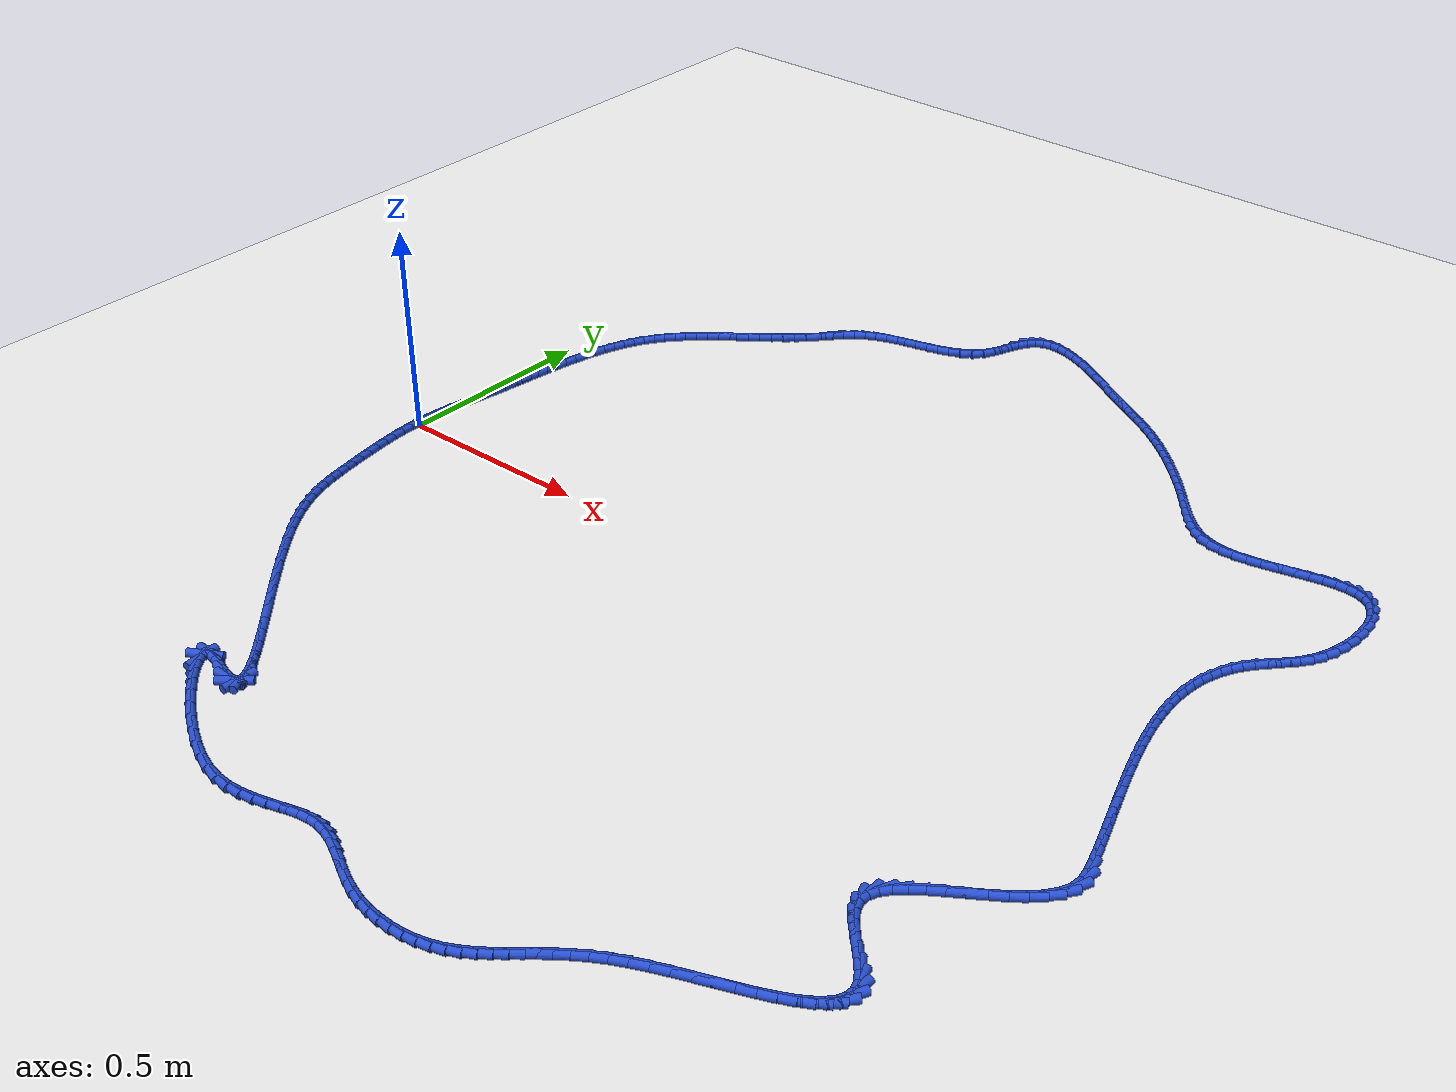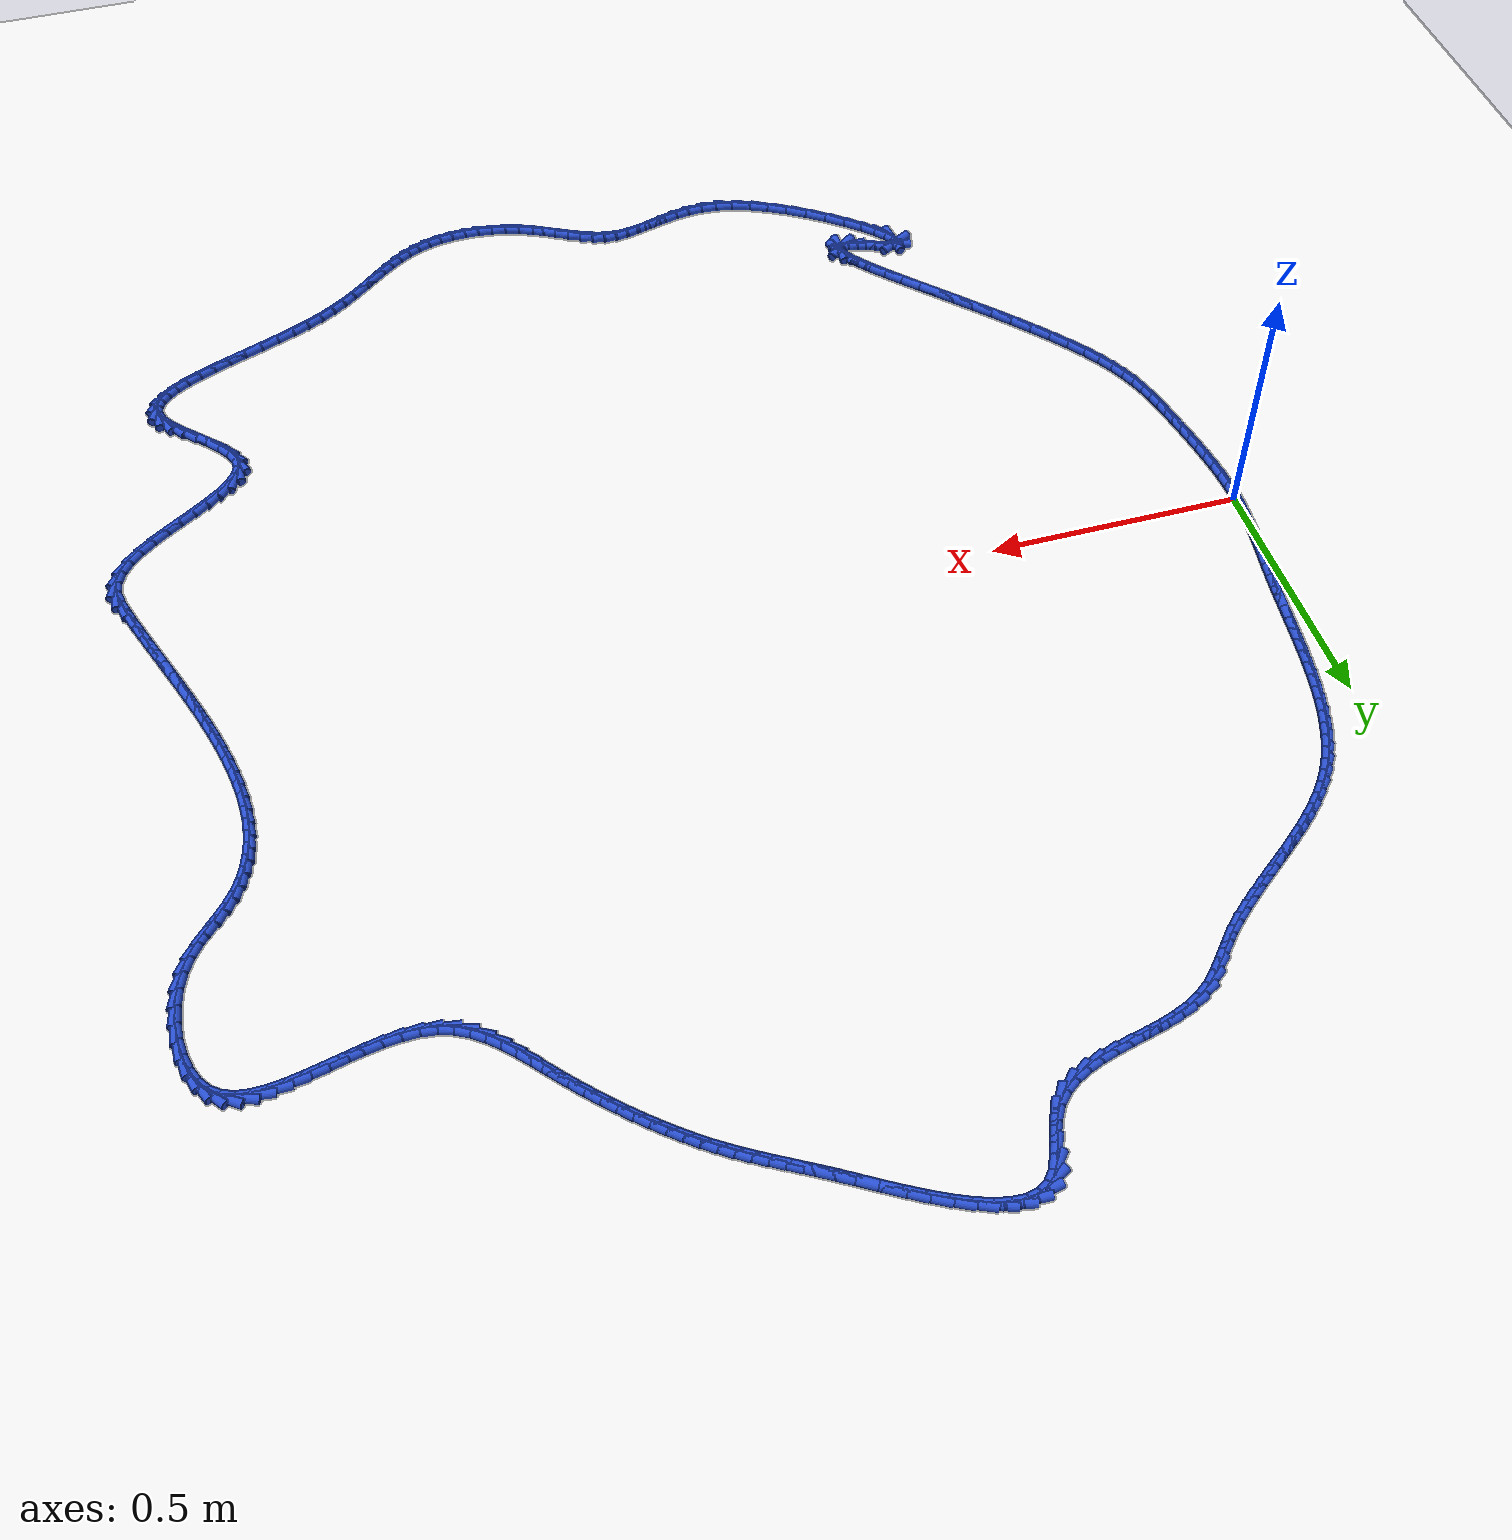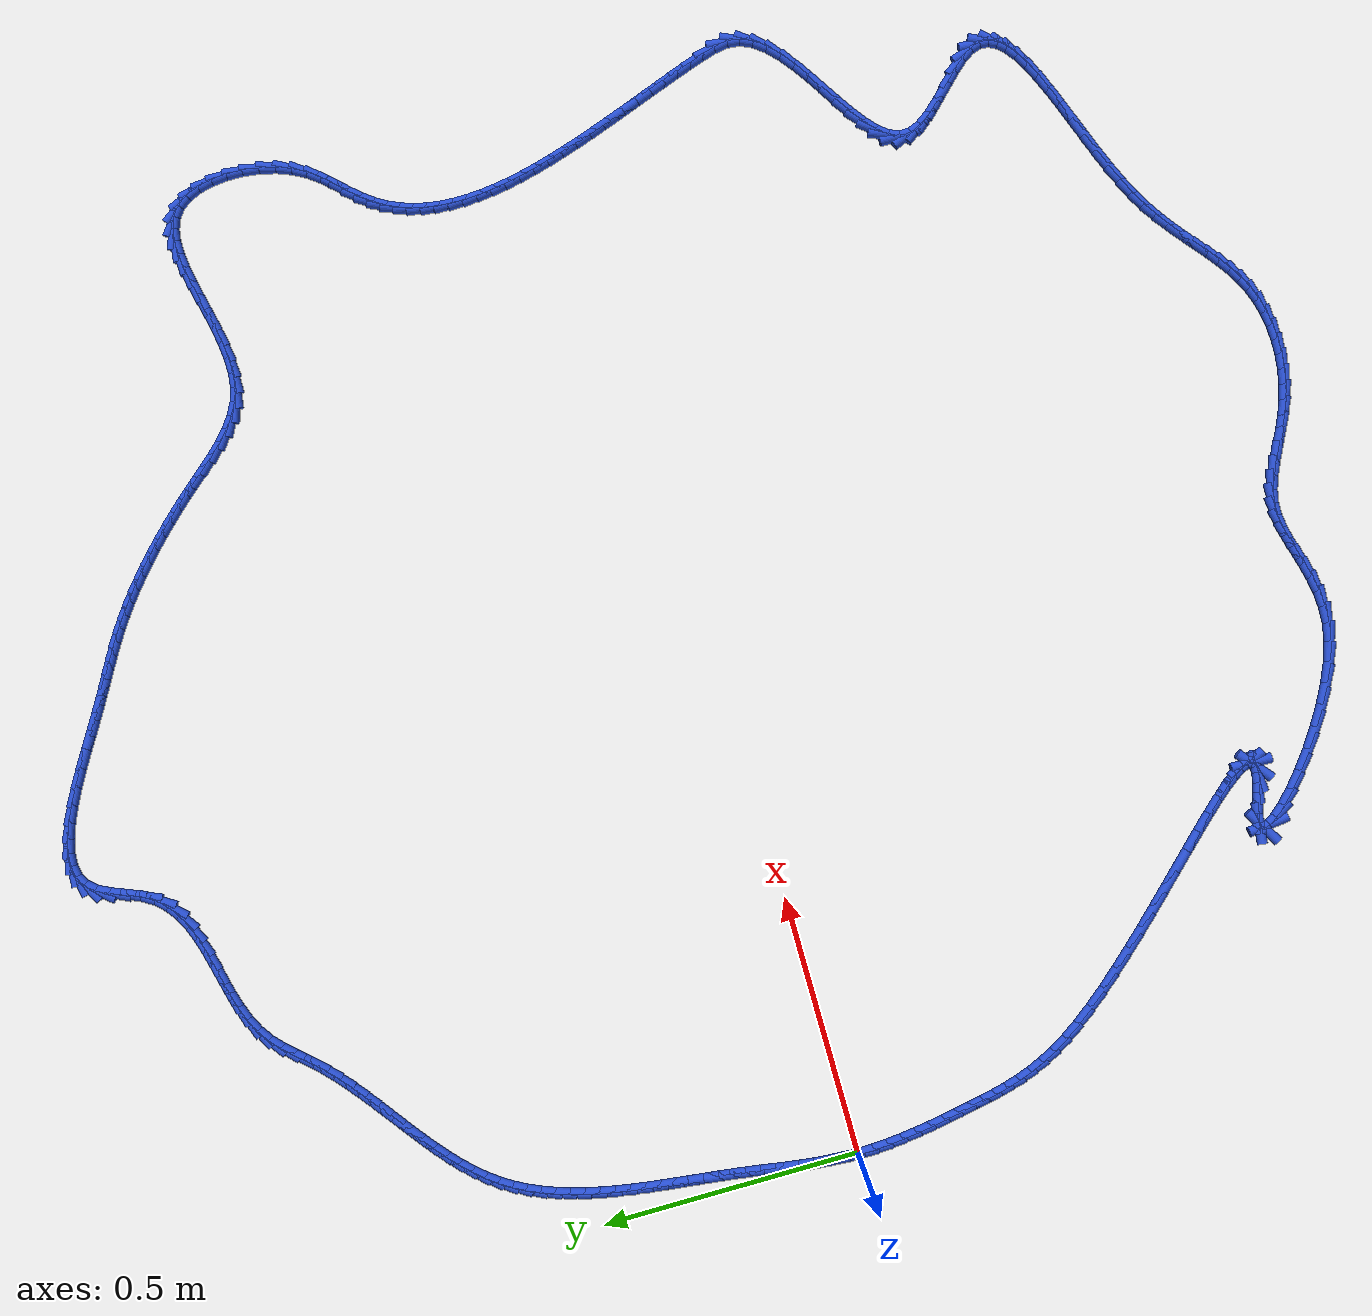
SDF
<sdf version="1.6">
 <world name="default">
  <light name="sun" type="directional">
   <pose>0 0 10 0 -0 0</pose>
   <diffuse>0.8 0.8 0.8 1</diffuse>
   <specular>0.2 0.2 0.2 1</specular>
   <attenuation>
    <range>1000</range>
    <constant>0.9</constant>
    <linear>0.01</linear>
    <quadratic>0.001</quadratic>
   </attenuation>
   <direction>-0.5 0.1 -0.9</direction>
  </light>
  <model name="ground_plane">
   <static>1</static>
   <link name="link">
    <collision name="collision">
     <geometry><plane><normal>0 0 1</normal><size>100 100</size></plane></geometry>
     <surface><friction><ode><mu>100</mu><mu2>50</mu2></ode></friction></surface>
    </collision>
    <visual name="visual">
     <cast_shadows>0</cast_shadows>
     <geometry><plane><normal>0 0 1</normal><size>100 100</size></plane></geometry>
     <material>
      <script><uri>file://media/materials/scripts/gazebo.material</uri><name>Gazebo/WhiteGlow</name></script>
     </material>
    </visual>
   </link>
  </model>
  <gravity>0 0 -9.8</gravity>
  <magnetic_field>6e-06 2.3e-05 -4.2e-05</magnetic_field>
  <atmosphere type="adiabatic"/>
  <physics name="default_physics" default="0" type="ode">
   <max_step_size>0.001</max_step_size>
   <real_time_factor>1</real_time_factor>
   <real_time_update_rate>1000</real_time_update_rate>
  </physics>
  <scene><ambient>0.4 0.4 0.4 1</ambient><background>0.7 0.7 0.7 1</background><shadows>1</shadows></scene>
  <spherical_coordinates>
   <surface_model>EARTH_WGS84</surface_model>
   <latitude_deg>0</latitude_deg>
   <longitude_deg>0</longitude_deg>
   <elevation>0</elevation>
   <heading_deg>0</heading_deg>
  </spherical_coordinates>
  <model name="line">
   <link name="link_0">
    <pose>8.673617379884035e-18 -6.938893903907228e-18 0.01 0 1.57 1.5409718841521143</pose>
    <collision name="collision">
     <geometry><cylinder><radius>0.01</radius><length>0.08</length></cylinder></geometry>
    </collision>
    <visual name="visual">
     <material>
      <script><name>Gazebo/Blue</name><uri>file://media/materials/scripts/gazebo.material</uri></script>
     </material>
     <geometry><cylinder><radius>0.01</radius><length>0.08</length></cylinder></geometry>
    </visual>
   </link>
   <link name="link_1">
    <pose>0.0008459314227873267 0.02835528563312401 0.01 0 1.57 1.5014154609786812</pose>
    <collision name="collision">
     <geometry><cylinder><radius>0.01</radius><length>0.08</length></cylinder></geometry>
    </collision>
    <visual name="visual">
     <material>
      <script><name>Gazebo/Blue</name><uri>file://media/materials/scripts/gazebo.material</uri></script>
     </material>
     <geometry><cylinder><radius>0.01</radius><length>0.08</length></cylinder></geometry>
    </visual>
   </link>
   <link name="link_2">
    <pose>0.0028027597509173562 0.05651416535578049 0.01 0 1.57 1.4691418552698836</pose>
    <collision name="collision">
     <geometry><cylinder><radius>0.01</radius><length>0.08</length></cylinder></geometry>
    </collision>
    <visual name="visual">
     <material>
      <script><name>Gazebo/Blue</name><uri>file://media/materials/scripts/gazebo.material</uri></script>
     </material>
     <geometry><cylinder><radius>0.01</radius><length>0.08</length></cylinder></geometry>
    </visual>
   </link>
   <link name="link_3">
    <pose>0.0056630419423527945 0.08455447668830844 0.01 0 1.57 1.4444604171441804</pose>
    <collision name="collision">
     <geometry><cylinder><radius>0.01</radius><length>0.08</length></cylinder></geometry>
    </collision>
    <visual name="visual">
     <material>
      <script><name>Gazebo/Blue</name><uri>file://media/materials/scripts/gazebo.material</uri></script>
     </material>
     <geometry><cylinder><radius>0.01</radius><length>0.08</length></cylinder></geometry>
    </visual>
   </link>
   <link name="link_4">
    <pose>0.009219334955056339 0.11255405715104687 0.01 0 1.57 1.4275146693953007</pose>
    <collision name="collision">
     <geometry><cylinder><radius>0.01</radius><length>0.08</length></cylinder></geometry>
    </collision>
    <visual name="visual">
     <material>
      <script><name>Gazebo/Blue</name><uri>file://media/materials/scripts/gazebo.material</uri></script>
     </material>
     <geometry><cylinder><radius>0.01</radius><length>0.08</length></cylinder></geometry>
    </visual>
   </link>
   <link name="link_5">
    <pose>0.01326419574699068 0.14059074426433482 0.01 0 1.57 1.4183217091300717</pose>
    <collision name="collision">
     <geometry><cylinder><radius>0.01</radius><length>0.08</length></cylinder></geometry>
    </collision>
    <visual name="visual">
     <material>
      <script><name>Gazebo/Blue</name><uri>file://media/materials/scripts/gazebo.material</uri></script>
     </material>
     <geometry><cylinder><radius>0.01</radius><length>0.08</length></cylinder></geometry>
    </visual>
   </link>
   <link name="link_6">
    <pose>0.01759018127611853 0.16874237554851132 0.01 0 1.57 1.4168035609285206</pose>
    <collision name="collision">
     <geometry><cylinder><radius>0.01</radius><length>0.08</length></cylinder></geometry>
    </collision>
    <visual name="visual">
     <material>
      <script><name>Gazebo/Blue</name><uri>file://media/materials/scripts/gazebo.material</uri></script>
     </material>
     <geometry><cylinder><radius>0.01</radius><length>0.08</length></cylinder></geometry>
    </visual>
   </link>
   <link name="link_7">
    <pose>0.021989848500402573 0.19708678852391542 0.01 0 1.57 1.422807046329848</pose>
    <collision name="collision">
     <geometry><cylinder><radius>0.01</radius><length>0.08</length></cylinder></geometry>
    </collision>
    <visual name="visual">
     <material>
      <script><name>Gazebo/Blue</name><uri>file://media/materials/scripts/gazebo.material</uri></script>
     </material>
     <geometry><cylinder><radius>0.01</radius><length>0.08</length></cylinder></geometry>
    </visual>
   </link>
   <link name="link_8">
    <pose>0.02625575437780551 0.22570182071088613 0.01 0 1.57 1.4349243816880823</pose>
    <collision name="collision">
     <geometry><cylinder><radius>0.01</radius><length>0.08</length></cylinder></geometry>
    </collision>
    <visual name="visual">
     <material>
      <script><name>Gazebo/Blue</name><uri>file://media/materials/scripts/gazebo.material</uri></script>
     </material>
     <geometry><cylinder><radius>0.01</radius><length>0.08</length></cylinder></geometry>
    </visual>
   </link>
   <link name="link_9">
    <pose>0.030213189890216003 0.2546485801065612 0.01 0 1.57 1.4450535467283119</pose>
    <collision name="collision">
     <geometry><cylinder><radius>0.01</radius><length>0.08</length></cylinder></geometry>
    </collision>
    <visual name="visual">
     <material>
      <script><name>Gazebo/Blue</name><uri>file://media/materials/scripts/gazebo.material</uri></script>
     </material>
     <geometry><cylinder><radius>0.01</radius><length>0.08</length></cylinder></geometry>
    </visual>
   </link>
   <link name="link_10">
    <pose>0.0339077659649885 0.28387557481361697 0.01 0 1.57 1.4500570326473867</pose>
    <collision name="collision">
     <geometry><cylinder><radius>0.01</radius><length>0.08</length></cylinder></geometry>
    </collision>
    <visual name="visual">
     <material>
      <script><name>Gazebo/Blue</name><uri>file://media/materials/scripts/gazebo.material</uri></script>
     </material>
     <geometry><cylinder><radius>0.01</radius><length>0.08</length></cylinder></geometry>
    </visual>
   </link>
   <link name="link_11">
    <pose>0.03747597874428108 0.31328486382376375 0.01 0 1.57 1.4500503241573974</pose>
    <collision name="collision">
     <geometry><cylinder><radius>0.01</radius><length>0.08</length></cylinder></geometry>
    </collision>
    <visual name="visual">
     <material>
      <script><name>Gazebo/Blue</name><uri>file://media/materials/scripts/gazebo.material</uri></script>
     </material>
     <geometry><cylinder><radius>0.01</radius><length>0.08</length></cylinder></geometry>
    </visual>
   </link>
   <link name="link_12">
    <pose>0.04105460917173479 0.34277836057395095 0.01 0 1.57 1.4450762870016227</pose>
    <collision name="collision">
     <geometry><cylinder><radius>0.01</radius><length>0.08</length></cylinder></geometry>
    </collision>
    <visual name="visual">
     <material>
      <script><name>Gazebo/Blue</name><uri>file://media/materials/scripts/gazebo.material</uri></script>
     </material>
     <geometry><cylinder><radius>0.01</radius><length>0.08</length></cylinder></geometry>
    </visual>
   </link>
   <link name="link_13">
    <pose>0.044780438190990667 0.3722579785011281 0.01 0 1.57 1.4350971684538663</pose>
    <collision name="collision">
     <geometry><cylinder><radius>0.01</radius><length>0.08</length></cylinder></geometry>
    </collision>
    <visual name="visual">
     <material>
      <script><name>Gazebo/Blue</name><uri>file://media/materials/scripts/gazebo.material</uri></script>
     </material>
     <geometry><cylinder><radius>0.01</radius><length>0.08</length></cylinder></geometry>
    </visual>
   </link>
   <link name="link_14">
    <pose>0.048790246745689735 0.40162563104224486 0.01 0 1.57 1.419997435423446</pose>
    <collision name="collision">
     <geometry><cylinder><radius>0.01</radius><length>0.08</length></cylinder></geometry>
    </collision>
    <visual name="visual">
     <material>
      <script><name>Gazebo/Blue</name><uri>file://media/materials/scripts/gazebo.material</uri></script>
     </material>
     <geometry><cylinder><radius>0.01</radius><length>0.08</length></cylinder></geometry>
    </visual>
   </link>
   <link name="link_15">
    <pose>0.05322081577947305 0.43078323163425064 0.01 0 1.57 1.399587688361434</pose>
    <collision name="collision">
     <geometry><cylinder><radius>0.01</radius><length>0.08</length></cylinder></geometry>
    </collision>
    <visual name="visual">
     <material>
      <script><name>Gazebo/Blue</name><uri>file://media/materials/scripts/gazebo.material</uri></script>
     </material>
     <geometry><cylinder><radius>0.01</radius><length>0.08</length></cylinder></geometry>
    </visual>
   </link>
   <link name="link_16">
    <pose>0.05820892623598163 0.4596326937140951 0.01 0 1.57 1.3736108628218646</pose>
    <collision name="collision">
     <geometry><cylinder><radius>0.01</radius><length>0.08</length></cylinder></geometry>
    </collision>
    <visual name="visual">
     <material>
      <script><name>Gazebo/Blue</name><uri>file://media/materials/scripts/gazebo.material</uri></script>
     </material>
     <geometry><cylinder><radius>0.01</radius><length>0.08</length></cylinder></geometry>
    </visual>
   </link>
   <link name="link_17">
    <pose>0.06389135905885654 0.4880759307187279 0.01 0 1.57 1.3417526721261681</pose>
    <collision name="collision">
     <geometry><cylinder><radius>0.01</radius><length>0.08</length></cylinder></geometry>
    </collision>
    <visual name="visual">
     <material>
      <script><name>Gazebo/Blue</name><uri>file://media/materials/scripts/gazebo.material</uri></script>
     </material>
     <geometry><cylinder><radius>0.01</radius><length>0.08</length></cylinder></geometry>
    </visual>
   </link>
   <link name="link_18">
    <pose>0.07040489519173876 0.5160148560850982 0.01 0 1.57 1.3036590968623252</pose>
    <collision name="collision">
     <geometry><cylinder><radius>0.01</radius><length>0.08</length></cylinder></geometry>
    </collision>
    <visual name="visual">
     <material>
      <script><name>Gazebo/Blue</name><uri>file://media/materials/scripts/gazebo.material</uri></script>
     </material>
     <geometry><cylinder><radius>0.01</radius><length>0.08</length></cylinder></geometry>
    </visual>
   </link>
   <link name="link_19">
    <pose>0.0778863155782694 0.543351383250156 0.01 0 1.57 1.2589645776523617</pose>
    <collision name="collision">
     <geometry><cylinder><radius>0.01</radius><length>0.08</length></cylinder></geometry>
    </collision>
    <visual name="visual">
     <material>
      <script><name>Gazebo/Blue</name><uri>file://media/materials/scripts/gazebo.material</uri></script>
     </material>
     <geometry><cylinder><radius>0.01</radius><length>0.08</length></cylinder></geometry>
    </visual>
   </link>
   <link name="link_20">
    <pose>0.08647240116208943 0.5699874256508505 0.01 0 1.57 1.2073350757554027</pose>
    <collision name="collision">
     <geometry><cylinder><radius>0.01</radius><length>0.08</length></cylinder></geometry>
    </collision>
    <visual name="visual">
     <material>
      <script><name>Gazebo/Blue</name><uri>file://media/materials/scripts/gazebo.material</uri></script>
     </material>
     <geometry><cylinder><radius>0.01</radius><length>0.08</length></cylinder></geometry>
    </visual>
   </link>
   <link name="link_21">
    <pose>0.09629993288683994 0.5958248967241314 0.01 0 1.57 1.1485296295350298</pose>
    <collision name="collision">
     <geometry><cylinder><radius>0.01</radius><length>0.08</length></cylinder></geometry>
    </collision>
    <visual name="visual">
     <material>
      <script><name>Gazebo/Blue</name><uri>file://media/materials/scripts/gazebo.material</uri></script>
     </material>
     <geometry><cylinder><radius>0.01</radius><length>0.08</length></cylinder></geometry>
    </visual>
   </link>
   <link name="link_22">
    <pose>0.10750569169616196 0.6207657099069485 0.01 0 1.57 1.0824813366347996</pose>
    <collision name="collision">
     <geometry><cylinder><radius>0.01</radius><length>0.08</length></cylinder></geometry>
    </collision>
    <visual name="visual">
     <material>
      <script><name>Gazebo/Blue</name><uri>file://media/materials/scripts/gazebo.material</uri></script>
     </material>
     <geometry><cylinder><radius>0.01</radius><length>0.08</length></cylinder></geometry>
    </visual>
   </link>
   <link name="link_23">
    <pose>0.12022645853369647 0.6447117786362508 0.01 0 1.57 1.0093925835638657</pose>
    <collision name="collision">
     <geometry><cylinder><radius>0.01</radius><length>0.08</length></cylinder></geometry>
    </collision>
    <visual name="visual">
     <material>
      <script><name>Gazebo/Blue</name><uri>file://media/materials/scripts/gazebo.material</uri></script>
     </material>
     <geometry><cylinder><radius>0.01</radius><length>0.08</length></cylinder></geometry>
    </visual>
   </link>
   <link name="link_24">
    <pose>0.13459901434308458 0.6675650163489882 0.01 0 1.57 0.9320099316146373</pose>
    <collision name="collision">
     <geometry><cylinder><radius>0.01</radius><length>0.08</length></cylinder></geometry>
    </collision>
    <visual name="visual">
     <material>
      <script><name>Gazebo/Blue</name><uri>file://media/materials/scripts/gazebo.material</uri></script>
     </material>
     <geometry><cylinder><radius>0.01</radius><length>0.08</length></cylinder></geometry>
    </visual>
   </link>
   <link name="link_25">
    <pose>0.1507126961604763 0.6892622936724273 0.01 0 1.57 0.8615453477317301</pose>
    <collision name="collision">
     <geometry><cylinder><radius>0.01</radius><length>0.08</length></cylinder></geometry>
    </collision>
    <visual name="visual">
     <material>
      <script><name>Gazebo/Blue</name><uri>file://media/materials/scripts/gazebo.material</uri></script>
     </material>
     <geometry><cylinder><radius>0.01</radius><length>0.08</length></cylinder></geometry>
    </visual>
   </link>
   <link name="link_26">
    <pose>0.16843065863937007 0.7099071348889575 0.01 0 1.57 0.8015421602711079</pose>
    <collision name="collision">
     <geometry><cylinder><radius>0.01</radius><length>0.08</length></cylinder></geometry>
    </collision>
    <visual name="visual">
     <material>
      <script><name>Gazebo/Blue</name><uri>file://media/materials/scripts/gazebo.material</uri></script>
     </material>
     <geometry><cylinder><radius>0.01</radius><length>0.08</length></cylinder></geometry>
    </visual>
   </link>
   <link name="link_27">
    <pose>0.18754872793895072 0.7296526726524946 0.01 0 1.57 0.7519712115304293</pose>
    <collision name="collision">
     <geometry><cylinder><radius>0.01</radius><length>0.08</length></cylinder></geometry>
    </collision>
    <visual name="visual">
     <material>
      <script><name>Gazebo/Blue</name><uri>file://media/materials/scripts/gazebo.material</uri></script>
     </material>
     <geometry><cylinder><radius>0.01</radius><length>0.08</length></cylinder></geometry>
    </visual>
   </link>
   <link name="link_28">
    <pose>0.20786271890854083 0.7486520479501848 0.01 0 1.57 0.7125176106189945</pose>
    <collision name="collision">
     <geometry><cylinder><radius>0.01</radius><length>0.08</length></cylinder></geometry>
    </collision>
    <visual name="visual">
     <material>
      <script><name>Gazebo/Blue</name><uri>file://media/materials/scripts/gazebo.material</uri></script>
     </material>
     <geometry><cylinder><radius>0.01</radius><length>0.08</length></cylinder></geometry>
    </visual>
   </link>
   <link name="link_29">
    <pose>0.22916844639746245 0.7670584017691744 0.01 0 1.57 0.682744023144074</pose>
    <collision name="collision">
     <geometry><cylinder><radius>0.01</radius><length>0.08</length></cylinder></geometry>
    </collision>
    <visual name="visual">
     <material>
      <script><name>Gazebo/Blue</name><uri>file://media/materials/scripts/gazebo.material</uri></script>
     </material>
     <geometry><cylinder><radius>0.01</radius><length>0.08</length></cylinder></geometry>
    </visual>
   </link>
   <link name="link_30">
    <pose>0.25126172525503826 0.7850248750966101 0.01 0 1.57 0.6622055635386376</pose>
    <collision name="collision">
     <geometry><cylinder><radius>0.01</radius><length>0.08</length></cylinder></geometry>
    </collision>
    <visual name="visual">
     <material>
      <script><name>Gazebo/Blue</name><uri>file://media/materials/scripts/gazebo.material</uri></script>
     </material>
     <geometry><cylinder><radius>0.01</radius><length>0.08</length></cylinder></geometry>
    </visual>
   </link>
   <link name="link_31">
    <pose>0.2739383703305906 0.8027046089196382 0.01 0 1.57 0.6505219156034365</pose>
    <collision name="collision">
     <geometry><cylinder><radius>0.01</radius><length>0.08</length></cylinder></geometry>
    </collision>
    <visual name="visual">
     <material>
      <script><name>Gazebo/Blue</name><uri>file://media/materials/scripts/gazebo.material</uri></script>
     </material>
     <geometry><cylinder><radius>0.01</radius><length>0.08</length></cylinder></geometry>
    </visual>
   </link>
   <link name="link_32">
    <pose>0.2969941964734417 0.8202507442254046 0.01 0 1.57 0.6474170595563229</pose>
    <collision name="collision">
     <geometry><cylinder><radius>0.01</radius><length>0.08</length></cylinder></geometry>
    </collision>
    <visual name="visual">
     <material>
      <script><name>Gazebo/Blue</name><uri>file://media/materials/scripts/gazebo.material</uri></script>
     </material>
     <geometry><cylinder><radius>0.01</radius><length>0.08</length></cylinder></geometry>
    </visual>
   </link>
   <link name="link_33">
    <pose>0.32022501853291413 0.8378164220010559 0.01 0 1.57 0.6527360985399905</pose>
    <collision name="collision">
     <geometry><cylinder><radius>0.01</radius><length>0.08</length></cylinder></geometry>
    </collision>
    <visual name="visual">
     <material>
      <script><name>Gazebo/Blue</name><uri>file://media/materials/scripts/gazebo.material</uri></script>
     </material>
     <geometry><cylinder><radius>0.01</radius><length>0.08</length></cylinder></geometry>
    </visual>
   </link>
   <link name="link_34">
    <pose>0.3434266513583301 0.8555547832337383 0.01 0 1.57 0.666445452769485</pose>
    <collision name="collision">
     <geometry><cylinder><radius>0.01</radius><length>0.08</length></cylinder></geometry>
    </collision>
    <visual name="visual">
     <material>
      <script><name>Gazebo/Blue</name><uri>file://media/materials/scripts/gazebo.material</uri></script>
     </material>
     <geometry><cylinder><radius>0.01</radius><length>0.08</length></cylinder></geometry>
    </visual>
   </link>
   <link name="link_35">
    <pose>0.36639490979901185 0.873618968910598 0.01 0 1.57 0.6886190538065011</pose>
    <collision name="collision">
     <geometry><cylinder><radius>0.01</radius><length>0.08</length></cylinder></geometry>
    </collision>
    <visual name="visual">
     <material>
      <script><name>Gazebo/Blue</name><uri>file://media/materials/scripts/gazebo.material</uri></script>
     </material>
     <geometry><cylinder><radius>0.01</radius><length>0.08</length></cylinder></geometry>
    </visual>
   </link>
   <link name="link_36">
    <pose>0.38892560870428217 0.8921621200187818 0.01 0 1.57 0.7194098844265059</pose>
    <collision name="collision">
     <geometry><cylinder><radius>0.01</radius><length>0.08</length></cylinder></geometry>
    </collision>
    <visual name="visual">
     <material>
      <script><name>Gazebo/Blue</name><uri>file://media/materials/scripts/gazebo.material</uri></script>
     </material>
     <geometry><cylinder><radius>0.01</radius><length>0.08</length></cylinder></geometry>
    </visual>
   </link>
   <link name="link_37">
    <pose>0.41081456292346313 0.9113373775454356 0.01 0 1.57 0.7590036536996266</pose>
    <collision name="collision">
     <geometry><cylinder><radius>0.01</radius><length>0.08</length></cylinder></geometry>
    </collision>
    <visual name="visual">
     <material>
      <script><name>Gazebo/Blue</name><uri>file://media/materials/scripts/gazebo.material</uri></script>
     </material>
     <geometry><cylinder><radius>0.01</radius><length>0.08</length></cylinder></geometry>
    </visual>
   </link>
   <link name="link_38">
    <pose>0.4318575873058772 0.9312978824777056 0.01 0 1.57 0.8073656967837953</pose>
    <collision name="collision">
     <geometry><cylinder><radius>0.01</radius><length>0.08</length></cylinder></geometry>
    </collision>
    <visual name="visual">
     <material>
      <script><name>Gazebo/Blue</name><uri>file://media/materials/scripts/gazebo.material</uri></script>
     </material>
     <geometry><cylinder><radius>0.01</radius><length>0.08</length></cylinder></geometry>
    </visual>
   </link>
   <link name="link_39">
    <pose>0.4518541055050259 0.9521928298354162 0.01 0 1.57 0.8433917566804576</pose>
    <collision name="collision">
     <geometry><cylinder><radius>0.01</radius><length>0.08</length></cylinder></geometry>
    </collision>
    <visual name="visual">
     <material>
      <script><name>Gazebo/Blue</name><uri>file://media/materials/scripts/gazebo.material</uri></script>
     </material>
     <geometry><cylinder><radius>0.01</radius><length>0.08</length></cylinder></geometry>
    </visual>
   </link>
   <link name="link_40">
    <pose>0.4710175889915194 0.9737186831863092 0.01 0 1.57 0.8263139130859298</pose>
    <collision name="collision">
     <geometry><cylinder><radius>0.01</radius><length>0.08</length></cylinder></geometry>
    </collision>
    <visual name="visual">
     <material>
      <script><name>Gazebo/Blue</name><uri>file://media/materials/scripts/gazebo.material</uri></script>
     </material>
     <geometry><cylinder><radius>0.01</radius><length>0.08</length></cylinder></geometry>
    </visual>
   </link>
   <link name="link_41">
    <pose>0.49035376507891293 0.9947056314231364 0.01 0 1.57 0.7496333584018579</pose>
    <collision name="collision">
     <geometry><cylinder><radius>0.01</radius><length>0.08</length></cylinder></geometry>
    </collision>
    <visual name="visual">
     <material>
      <script><name>Gazebo/Blue</name><uri>file://media/materials/scripts/gazebo.material</uri></script>
     </material>
     <geometry><cylinder><radius>0.01</radius><length>0.08</length></cylinder></geometry>
    </visual>
   </link>
   <link name="link_42">
    <pose>0.5109577489463684 1.013886124248821 0.01 0 1.57 0.6141857565335127</pose>
    <collision name="collision">
     <geometry><cylinder><radius>0.01</radius><length>0.08</length></cylinder></geometry>
    </collision>
    <visual name="visual">
     <material>
      <script><name>Gazebo/Blue</name><uri>file://media/materials/scripts/gazebo.material</uri></script>
     </material>
     <geometry><cylinder><radius>0.01</radius><length>0.08</length></cylinder></geometry>
    </visual>
   </link>
   <link name="link_43">
    <pose>0.5338774827811377 1.0300483785491392 0.01 0 1.57 0.4709693728344743</pose>
    <collision name="collision">
     <geometry><cylinder><radius>0.01</radius><length>0.08</length></cylinder></geometry>
    </collision>
    <visual name="visual">
     <material>
      <script><name>Gazebo/Blue</name><uri>file://media/materials/scripts/gazebo.material</uri></script>
     </material>
     <geometry><cylinder><radius>0.01</radius><length>0.08</length></cylinder></geometry>
    </visual>
   </link>
   <link name="link_44">
    <pose>0.5593030720194687 1.0429947325749651 0.01 0 1.57 0.3636248641162891</pose>
    <collision name="collision">
     <geometry><cylinder><radius>0.01</radius><length>0.08</length></cylinder></geometry>
    </collision>
    <visual name="visual">
     <material>
      <script><name>Gazebo/Blue</name><uri>file://media/materials/scripts/gazebo.material</uri></script>
     </material>
     <geometry><cylinder><radius>0.01</radius><length>0.08</length></cylinder></geometry>
    </visual>
   </link>
   <link name="link_45">
    <pose>0.5866767148247114 1.0534116890101701 0.01 0 1.57 0.2908831301023856</pose>
    <collision name="collision">
     <geometry><cylinder><radius>0.01</radius><length>0.08</length></cylinder></geometry>
    </collision>
    <visual name="visual">
     <material>
      <script><name>Gazebo/Blue</name><uri>file://media/materials/scripts/gazebo.material</uri></script>
     </material>
     <geometry><cylinder><radius>0.01</radius><length>0.08</length></cylinder></geometry>
    </visual>
   </link>
   <link name="link_46">
    <pose>0.6154155519577993 1.0620153730129664 0.01 0 1.57 0.2489994214945915</pose>
    <collision name="collision">
     <geometry><cylinder><radius>0.01</radius><length>0.08</length></cylinder></geometry>
    </collision>
    <visual name="visual">
     <material>
      <script><name>Gazebo/Blue</name><uri>file://media/materials/scripts/gazebo.material</uri></script>
     </material>
     <geometry><cylinder><radius>0.01</radius><length>0.08</length></cylinder></geometry>
    </visual>
   </link>
   <link name="link_47">
    <pose>0.6449367241796661 1.0695219097415671 0.01 0 1.57 0.23530824060760183</pose>
    <collision name="collision">
     <geometry><cylinder><radius>0.01</radius><length>0.08</length></cylinder></geometry>
    </collision>
    <visual name="visual">
     <material>
      <script><name>Gazebo/Blue</name><uri>file://media/materials/scripts/gazebo.material</uri></script>
     </material>
     <geometry><cylinder><radius>0.01</radius><length>0.08</length></cylinder></geometry>
    </visual>
   </link>
   <link name="link_48">
    <pose>0.6746573722512452 1.0766474243541837 0.01 0 1.57 0.24902645166853424</pose>
    <collision name="collision">
     <geometry><cylinder><radius>0.01</radius><length>0.08</length></cylinder></geometry>
    </collision>
    <visual name="visual">
     <material>
      <script><name>Gazebo/Blue</name><uri>file://media/materials/scripts/gazebo.material</uri></script>
     </material>
     <geometry><cylinder><radius>0.01</radius><length>0.08</length></cylinder></geometry>
    </visual>
   </link>
   <link name="link_49">
    <pose>0.70399463693347 1.084108042009029 0.01 0 1.57 0.2914742317144534</pose>
    <collision name="collision">
     <geometry><cylinder><radius>0.01</radius><length>0.08</length></cylinder></geometry>
    </collision>
    <visual name="visual">
     <material>
      <script><name>Gazebo/Blue</name><uri>file://media/materials/scripts/gazebo.material</uri></script>
     </material>
     <geometry><cylinder><radius>0.01</radius><length>0.08</length></cylinder></geometry>
    </visual>
   </link>
   <link name="link_50">
    <pose>0.7323656589872739 1.092619887864315 0.01 0 1.57 0.3659740493499417</pose>
    <collision name="collision">
     <geometry><cylinder><radius>0.01</radius><length>0.08</length></cylinder></geometry>
    </collision>
    <visual name="visual">
     <material>
      <script><name>Gazebo/Blue</name><uri>file://media/materials/scripts/gazebo.material</uri></script>
     </material>
     <geometry><cylinder><radius>0.01</radius><length>0.08</length></cylinder></geometry>
    </visual>
   </link>
   <link name="link_51">
    <pose>0.7591875791735904 1.102899087078254 0.01 0 1.57 0.4770900159526874</pose>
    <collision name="collision">
     <geometry><cylinder><radius>0.01</radius><length>0.08</length></cylinder></geometry>
    </collision>
    <visual name="visual">
     <material>
      <script><name>Gazebo/Blue</name><uri>file://media/materials/scripts/gazebo.material</uri></script>
     </material>
     <geometry><cylinder><radius>0.01</radius><length>0.08</length></cylinder></geometry>
    </visual>
   </link>
   <link name="link_52">
    <pose>0.7838775382533529 1.1156617648090588 0.01 0 1.57 0.6282115546998763</pose>
    <collision name="collision">
     <geometry><cylinder><radius>0.01</radius><length>0.08</length></cylinder></geometry>
    </collision>
    <visual name="visual">
     <material>
      <script><name>Gazebo/Blue</name><uri>file://media/materials/scripts/gazebo.material</uri></script>
     </material>
     <geometry><cylinder><radius>0.01</radius><length>0.08</length></cylinder></geometry>
    </visual>
   </link>
   <link name="link_53">
    <pose>0.805852676987495 1.131624046214941 0.01 0 1.57 0.8165263877236337</pose>
    <collision name="collision">
     <geometry><cylinder><radius>0.01</radius><length>0.08</length></cylinder></geometry>
    </collision>
    <visual name="visual">
     <material>
      <script><name>Gazebo/Blue</name><uri>file://media/materials/scripts/gazebo.material</uri></script>
     </material>
     <geometry><cylinder><radius>0.01</radius><length>0.08</length></cylinder></geometry>
    </visual>
   </link>
   <link name="link_54">
    <pose>0.8245301361369501 1.1515020564541134 0.01 0 1.57 1.0233464286361933</pose>
    <collision name="collision">
     <geometry><cylinder><radius>0.01</radius><length>0.08</length></cylinder></geometry>
    </collision>
    <visual name="visual">
     <material>
      <script><name>Gazebo/Blue</name><uri>file://media/materials/scripts/gazebo.material</uri></script>
     </material>
     <geometry><cylinder><radius>0.01</radius><length>0.08</length></cylinder></geometry>
    </visual>
   </link>
   <link name="link_55">
    <pose>0.8394029459800585 1.175899630236961 0.01 0 1.57 1.1618448366143228</pose>
    <collision name="collision">
     <geometry><cylinder><radius>0.01</radius><length>0.08</length></cylinder></geometry>
    </collision>
    <visual name="visual">
     <material>
      <script><name>Gazebo/Blue</name><uri>file://media/materials/scripts/gazebo.material</uri></script>
     </material>
     <geometry><cylinder><radius>0.01</radius><length>0.08</length></cylinder></geometry>
    </visual>
   </link>
   <link name="link_56">
    <pose>0.8513245303279926 1.2034076866006225 0.01 0 1.57 1.1899298419403797</pose>
    <collision name="collision">
     <geometry><cylinder><radius>0.01</radius><length>0.08</length></cylinder></geometry>
    </collision>
    <visual name="visual">
     <material>
      <script><name>Gazebo/Blue</name><uri>file://media/materials/scripts/gazebo.material</uri></script>
     </material>
     <geometry><cylinder><radius>0.01</radius><length>0.08</length></cylinder></geometry>
    </visual>
   </link>
   <link name="link_57">
    <pose>0.8623239652482819 1.2308775826128562 0.01 0 1.57 1.1060880423296635</pose>
    <collision name="collision">
     <geometry><cylinder><radius>0.01</radius><length>0.08</length></cylinder></geometry>
    </collision>
    <visual name="visual">
     <material>
      <script><name>Gazebo/Blue</name><uri>file://media/materials/scripts/gazebo.material</uri></script>
     </material>
     <geometry><cylinder><radius>0.01</radius><length>0.08</length></cylinder></geometry>
    </visual>
   </link>
   <link name="link_58">
    <pose>0.874469021169373 1.2551034209634182 0.01 0 1.57 0.8653335721720171</pose>
    <collision name="collision">
     <geometry><cylinder><radius>0.01</radius><length>0.08</length></cylinder></geometry>
    </collision>
    <visual name="visual">
     <material>
      <script><name>Gazebo/Blue</name><uri>file://media/materials/scripts/gazebo.material</uri></script>
     </material>
     <geometry><cylinder><radius>0.01</radius><length>0.08</length></cylinder></geometry>
    </visual>
   </link>
   <link name="link_59">
    <pose>0.8897334361672847 1.2730263441482286 0.01 0 1.57 0.5145881483495591</pose>
    <collision name="collision">
     <geometry><cylinder><radius>0.01</radius><length>0.08</length></cylinder></geometry>
    </collision>
    <visual name="visual">
     <material>
      <script><name>Gazebo/Blue</name><uri>file://media/materials/scripts/gazebo.material</uri></script>
     </material>
     <geometry><cylinder><radius>0.01</radius><length>0.08</length></cylinder></geometry>
    </visual>
   </link>
   <link name="link_60">
    <pose>0.9087058902195183 1.2837533308787963 0.01 0 1.57 0.19068192162095352</pose>
    <collision name="collision">
     <geometry><cylinder><radius>0.01</radius><length>0.08</length></cylinder></geometry>
    </collision>
    <visual name="visual">
     <material>
      <script><name>Gazebo/Blue</name><uri>file://media/materials/scripts/gazebo.material</uri></script>
     </material>
     <geometry><cylinder><radius>0.01</radius><length>0.08</length></cylinder></geometry>
    </visual>
   </link>
   <link name="link_61">
    <pose>0.9309199560286426 1.2880412470084266 0.01 0 1.57 -0.05414138122336819</pose>
    <collision name="collision">
     <geometry><cylinder><radius>0.01</radius><length>0.08</length></cylinder></geometry>
    </collision>
    <visual name="visual">
     <material>
      <script><name>Gazebo/Blue</name><uri>file://media/materials/scripts/gazebo.material</uri></script>
     </material>
     <geometry><cylinder><radius>0.01</radius><length>0.08</length></cylinder></geometry>
    </visual>
   </link>
   <link name="link_62">
    <pose>0.9558826994892865 1.2866884074853446 0.01 0 1.57 -0.22380009340404106</pose>
    <collision name="collision">
     <geometry><cylinder><radius>0.01</radius><length>0.08</length></cylinder></geometry>
    </collision>
    <visual name="visual">
     <material>
      <script><name>Gazebo/Blue</name><uri>file://media/materials/scripts/gazebo.material</uri></script>
     </material>
     <geometry><cylinder><radius>0.01</radius><length>0.08</length></cylinder></geometry>
    </visual>
   </link>
   <link name="link_63">
    <pose>0.9831011864960802 1.2804931272577766 0.01 0 1.57 -0.3396212861030843</pose>
    <collision name="collision">
     <geometry><cylinder><radius>0.01</radius><length>0.08</length></cylinder></geometry>
    </collision>
    <visual name="visual">
     <material>
      <script><name>Gazebo/Blue</name><uri>file://media/materials/scripts/gazebo.material</uri></script>
     </material>
     <geometry><cylinder><radius>0.01</radius><length>0.08</length></cylinder></geometry>
    </visual>
   </link>
   <link name="link_64">
    <pose>1.0120824829436514 1.2702537212739475 0.01 0 1.57 -0.41933488223553456</pose>
    <collision name="collision">
     <geometry><cylinder><radius>0.01</radius><length>0.08</length></cylinder></geometry>
    </collision>
    <visual name="visual">
     <material>
      <script><name>Gazebo/Blue</name><uri>file://media/materials/scripts/gazebo.material</uri></script>
     </material>
     <geometry><cylinder><radius>0.01</radius><length>0.08</length></cylinder></geometry>
    </visual>
   </link>
   <link name="link_65">
    <pose>1.04233365472663 1.256768504482083 0.01 0 1.57 -0.47438349199871194</pose>
    <collision name="collision">
     <geometry><cylinder><radius>0.01</radius><length>0.08</length></cylinder></geometry>
    </collision>
    <visual name="visual">
     <material>
      <script><name>Gazebo/Blue</name><uri>file://media/materials/scripts/gazebo.material</uri></script>
     </material>
     <geometry><cylinder><radius>0.01</radius><length>0.08</length></cylinder></geometry>
    </visual>
   </link>
   <link name="link_66">
    <pose>1.0733617677396448 1.2408357918304096 0.01 0 1.57 -0.511632845165431</pose>
    <collision name="collision">
     <geometry><cylinder><radius>0.01</radius><length>0.08</length></cylinder></geometry>
    </collision>
    <visual name="visual">
     <material>
      <script><name>Gazebo/Blue</name><uri>file://media/materials/scripts/gazebo.material</uri></script>
     </material>
     <geometry><cylinder><radius>0.01</radius><length>0.08</length></cylinder></geometry>
    </visual>
   </link>
   <link name="link_67">
    <pose>1.1046738878773246 1.2232538982671524 0.01 0 1.57 -0.5349845233337354</pose>
    <collision name="collision">
     <geometry><cylinder><radius>0.01</radius><length>0.08</length></cylinder></geometry>
    </collision>
    <visual name="visual">
     <material>
      <script><name>Gazebo/Blue</name><uri>file://media/materials/scripts/gazebo.material</uri></script>
     </material>
     <geometry><cylinder><radius>0.01</radius><length>0.08</length></cylinder></geometry>
    </visual>
   </link>
   <link name="link_68">
    <pose>1.1357770810342989 1.2048211387405365 0.01 0 1.57 -0.5463123329642405</pose>
    <collision name="collision">
     <geometry><cylinder><radius>0.01</radius><length>0.08</length></cylinder></geometry>
    </collision>
    <visual name="visual">
     <material>
      <script><name>Gazebo/Blue</name><uri>file://media/materials/scripts/gazebo.material</uri></script>
     </material>
     <geometry><cylinder><radius>0.01</radius><length>0.08</length></cylinder></geometry>
    </visual>
   </link>
   <link name="link_69">
    <pose>1.1661784131051967 1.1863358281987884 0.01 0 1.57 -0.5458303144156916</pose>
    <collision name="collision">
     <geometry><cylinder><radius>0.01</radius><length>0.08</length></cylinder></geometry>
    </collision>
    <visual name="visual">
     <material>
      <script><name>Gazebo/Blue</name><uri>file://media/materials/scripts/gazebo.material</uri></script>
     </material>
     <geometry><cylinder><radius>0.01</radius><length>0.08</length></cylinder></geometry>
    </visual>
   </link>
   <link name="link_70">
    <pose>1.1953849499846465 1.1685962815901338 0.01 0 1.57 -0.5340886859717227</pose>
    <collision name="collision">
     <geometry><cylinder><radius>0.01</radius><length>0.08</length></cylinder></geometry>
    </collision>
    <visual name="visual">
     <material>
      <script><name>Gazebo/Blue</name><uri>file://media/materials/scripts/gazebo.material</uri></script>
     </material>
     <geometry><cylinder><radius>0.01</radius><length>0.08</length></cylinder></geometry>
    </visual>
   </link>
   <link name="link_71">
    <pose>1.2229783987465066 1.1522768935042664 0.01 0 1.57 -0.5232775400020789</pose>
    <collision name="collision">
     <geometry><cylinder><radius>0.01</radius><length>0.08</length></cylinder></geometry>
    </collision>
    <visual name="visual">
     <material>
      <script><name>Gazebo/Blue</name><uri>file://media/materials/scripts/gazebo.material</uri></script>
     </material>
     <geometry><cylinder><radius>0.01</radius><length>0.08</length></cylinder></geometry>
    </visual>
   </link>
   <link name="link_72">
    <pose>1.2490227786914303 1.1372513168399483 0.01 0 1.57 -0.5201498486941989</pose>
    <collision name="collision">
     <geometry><cylinder><radius>0.01</radius><length>0.08</length></cylinder></geometry>
    </collision>
    <visual name="visual">
     <material>
      <script><name>Gazebo/Blue</name><uri>file://media/materials/scripts/gazebo.material</uri></script>
     </material>
     <geometry><cylinder><radius>0.01</radius><length>0.08</length></cylinder></geometry>
    </visual>
   </link>
   <link name="link_73">
    <pose>1.2737738505533074 1.1230748726126907 0.01 0 1.57 -0.5261728567336321</pose>
    <collision name="collision">
     <geometry><cylinder><radius>0.01</radius><length>0.08</length></cylinder></geometry>
    </collision>
    <visual name="visual">
     <material>
      <script><name>Gazebo/Blue</name><uri>file://media/materials/scripts/gazebo.material</uri></script>
     </material>
     <geometry><cylinder><radius>0.01</radius><length>0.08</length></cylinder></geometry>
    </visual>
   </link>
   <link name="link_74">
    <pose>1.2974878639194398 1.109302070236542 0.01 0 1.57 -0.5421723792940519</pose>
    <collision name="collision">
     <geometry><cylinder><radius>0.01</radius><length>0.08</length></cylinder></geometry>
    </collision>
    <visual name="visual">
     <material>
      <script><name>Gazebo/Blue</name><uri>file://media/materials/scripts/gazebo.material</uri></script>
     </material>
     <geometry><cylinder><radius>0.01</radius><length>0.08</length></cylinder></geometry>
    </visual>
   </link>
   <link name="link_75">
    <pose>1.3204210683771311 1.0954874191255504 0.01 0 1.57 -0.5680603384175988</pose>
    <collision name="collision">
     <geometry><cylinder><radius>0.01</radius><length>0.08</length></cylinder></geometry>
    </collision>
    <visual name="visual">
     <material>
      <script><name>Gazebo/Blue</name><uri>file://media/materials/scripts/gazebo.material</uri></script>
     </material>
     <geometry><cylinder><radius>0.01</radius><length>0.08</length></cylinder></geometry>
    </visual>
   </link>
   <link name="link_76">
    <pose>1.3428297135136829 1.0811854286937643 0.01 0 1.57 -0.6015272644035145</pose>
    <collision name="collision">
     <geometry><cylinder><radius>0.01</radius><length>0.08</length></cylinder></geometry>
    </collision>
    <visual name="visual">
     <material>
      <script><name>Gazebo/Blue</name><uri>file://media/materials/scripts/gazebo.material</uri></script>
     </material>
     <geometry><cylinder><radius>0.01</radius><length>0.08</length></cylinder></geometry>
    </visual>
   </link>
   <link name="link_77">
    <pose>1.364939235853453 1.066009867217549 0.01 0 1.57 -0.6350300738799874</pose>
    <collision name="collision">
     <geometry><cylinder><radius>0.01</radius><length>0.08</length></cylinder></geometry>
    </collision>
    <visual name="visual">
     <material>
      <script><name>Gazebo/Blue</name><uri>file://media/materials/scripts/gazebo.material</uri></script>
     </material>
     <geometry><cylinder><radius>0.01</radius><length>0.08</length></cylinder></geometry>
    </visual>
   </link>
   <link name="link_78">
    <pose>1.3868079012809622 1.0498960010971938 0.01 0 1.57 -0.6663597182857146</pose>
    <collision name="collision">
     <geometry><cylinder><radius>0.01</radius><length>0.08</length></cylinder></geometry>
    </collision>
    <visual name="visual">
     <material>
      <script><name>Gazebo/Blue</name><uri>file://media/materials/scripts/gazebo.material</uri></script>
     </material>
     <geometry><cylinder><radius>0.01</radius><length>0.08</length></cylinder></geometry>
    </visual>
   </link>
   <link name="link_79">
    <pose>1.4084375502151882 1.0328876126860969 0.01 0 1.57 -0.695620978715392</pose>
    <collision name="collision">
     <geometry><cylinder><radius>0.01</radius><length>0.08</length></cylinder></geometry>
    </collision>
    <visual name="visual">
     <material>
      <script><name>Gazebo/Blue</name><uri>file://media/materials/scripts/gazebo.material</uri></script>
     </material>
     <geometry><cylinder><radius>0.01</radius><length>0.08</length></cylinder></geometry>
    </visual>
   </link>
   <link name="link_80">
    <pose>1.4298299793810063 1.0150285683689932 0.01 0 1.57 -0.722923203615513</pose>
    <collision name="collision">
     <geometry><cylinder><radius>0.01</radius><length>0.08</length></cylinder></geometry>
    </collision>
    <visual name="visual">
     <material>
      <script><name>Gazebo/Blue</name><uri>file://media/materials/scripts/gazebo.material</uri></script>
     </material>
     <geometry><cylinder><radius>0.01</radius><length>0.08</length></cylinder></geometry>
    </visual>
   </link>
   <link name="link_81">
    <pose>1.4509869855032915 0.996362734530617 0.01 0 1.57 -0.7483755914364022</pose>
    <collision name="collision">
     <geometry><cylinder><radius>0.01</radius><length>0.08</length></cylinder></geometry>
    </collision>
    <visual name="visual">
     <material>
      <script><name>Gazebo/Blue</name><uri>file://media/materials/scripts/gazebo.material</uri></script>
     </material>
     <geometry><cylinder><radius>0.01</radius><length>0.08</length></cylinder></geometry>
    </visual>
   </link>
   <link name="link_82">
    <pose>1.4719103653069192 0.9769339775557031 0.01 0 1.57 -0.7720849208307531</pose>
    <collision name="collision">
     <geometry><cylinder><radius>0.01</radius><length>0.08</length></cylinder></geometry>
    </collision>
    <visual name="visual">
     <material>
      <script><name>Gazebo/Blue</name><uri>file://media/materials/scripts/gazebo.material</uri></script>
     </material>
     <geometry><cylinder><radius>0.01</radius><length>0.08</length></cylinder></geometry>
    </visual>
   </link>
   <link name="link_83">
    <pose>1.4926019155167638 0.9567861638289865 0.01 0 1.57 -0.7941539271229002</pose>
    <collision name="collision">
     <geometry><cylinder><radius>0.01</radius><length>0.08</length></cylinder></geometry>
    </collision>
    <visual name="visual">
     <material>
      <script><name>Gazebo/Blue</name><uri>file://media/materials/scripts/gazebo.material</uri></script>
     </material>
     <geometry><cylinder><radius>0.01</radius><length>0.08</length></cylinder></geometry>
    </visual>
   </link>
   <link name="link_84">
    <pose>1.5130634328577 0.9359631597352014 0.01 0 1.57 -0.8146801944410829</pose>
    <collision name="collision">
     <geometry><cylinder><radius>0.01</radius><length>0.08</length></cylinder></geometry>
    </collision>
    <visual name="visual">
     <material>
      <script><name>Gazebo/Blue</name><uri>file://media/materials/scripts/gazebo.material</uri></script>
     </material>
     <geometry><cylinder><radius>0.01</radius><length>0.08</length></cylinder></geometry>
    </visual>
   </link>
   <link name="link_85">
    <pose>1.5332967140546034 0.9145088316590827 0.01 0 1.57 -0.83375544834641</pose>
    <collision name="collision">
     <geometry><cylinder><radius>0.01</radius><length>0.08</length></cylinder></geometry>
    </collision>
    <visual name="visual">
     <material>
      <script><name>Gazebo/Blue</name><uri>file://media/materials/scripts/gazebo.material</uri></script>
     </material>
     <geometry><cylinder><radius>0.01</radius><length>0.08</length></cylinder></geometry>
    </visual>
   </link>
   <link name="link_86">
    <pose>1.5533035558323482 0.8924670459853654 0.01 0 1.57 -0.8514618589272555</pose>
    <collision name="collision">
     <geometry><cylinder><radius>0.01</radius><length>0.08</length></cylinder></geometry>
    </collision>
    <visual name="visual">
     <material>
      <script><name>Gazebo/Blue</name><uri>file://media/materials/scripts/gazebo.material</uri></script>
     </material>
     <geometry><cylinder><radius>0.01</radius><length>0.08</length></cylinder></geometry>
    </visual>
   </link>
   <link name="link_87">
    <pose>1.5730858013282956 0.869881766142645 0.01 0 1.57 -0.8622722781272977</pose>
    <collision name="collision">
     <geometry><cylinder><radius>0.01</radius><length>0.08</length></cylinder></geometry>
    </collision>
    <visual name="visual">
     <material>
      <script><name>Gazebo/Blue</name><uri>file://media/materials/scripts/gazebo.material</uri></script>
     </material>
     <geometry><cylinder><radius>0.01</radius><length>0.08</length></cylinder></geometry>
    </visual>
   </link>
   <link name="link_88">
    <pose>1.592725311097373 0.8469642639692991 0.01 0 1.57 -0.8491846023364095</pose>
    <collision name="collision">
     <geometry><cylinder><radius>0.01</radius><length>0.08</length></cylinder></geometry>
    </collision>
    <visual name="visual">
     <material>
      <script><name>Gazebo/Blue</name><uri>file://media/materials/scripts/gazebo.material</uri></script>
     </material>
     <geometry><cylinder><radius>0.01</radius><length>0.08</length></cylinder></geometry>
    </visual>
   </link>
   <link name="link_89">
    <pose>1.6125481294542976 0.8244363751007748 0.01 0 1.57 -0.8079567585711803</pose>
    <collision name="collision">
     <geometry><cylinder><radius>0.01</radius><length>0.08</length></cylinder></geometry>
    </collision>
    <visual name="visual">
     <material>
      <script><name>Gazebo/Blue</name><uri>file://media/materials/scripts/gazebo.material</uri></script>
     </material>
     <geometry><cylinder><radius>0.01</radius><length>0.08</length></cylinder></geometry>
    </visual>
   </link>
   <link name="link_90">
    <pose>1.632926714791288 0.8031169823621721 0.01 0 1.57 -0.7358118674385963</pose>
    <collision name="collision">
     <geometry><cylinder><radius>0.01</radius><length>0.08</length></cylinder></geometry>
    </collision>
    <visual name="visual">
     <material>
      <script><name>Gazebo/Blue</name><uri>file://media/materials/scripts/gazebo.material</uri></script>
     </material>
     <geometry><cylinder><radius>0.01</radius><length>0.08</length></cylinder></geometry>
    </visual>
   </link>
   <link name="link_91">
    <pose>1.654233525500563 0.7838249685785925 0.01 0 1.57 -0.628910202059338</pose>
    <collision name="collision">
     <geometry><cylinder><radius>0.01</radius><length>0.08</length></cylinder></geometry>
    </collision>
    <visual name="visual">
     <material>
      <script><name>Gazebo/Blue</name><uri>file://media/materials/scripts/gazebo.material</uri></script>
     </material>
     <geometry><cylinder><radius>0.01</radius><length>0.08</length></cylinder></geometry>
    </visual>
   </link>
   <link name="link_92">
    <pose>1.6768410199743407 0.7673792165751351 0.01 0 1.57 -0.48452065969462255</pose>
    <collision name="collision">
     <geometry><cylinder><radius>0.01</radius><length>0.08</length></cylinder></geometry>
    </collision>
    <visual name="visual">
     <material>
      <script><name>Gazebo/Blue</name><uri>file://media/materials/scripts/gazebo.material</uri></script>
     </material>
     <geometry><cylinder><radius>0.01</radius><length>0.08</length></cylinder></geometry>
    </visual>
   </link>
   <link name="link_93">
    <pose>1.701121656604841 0.7545986091769015 0.01 0 1.57 -0.3056872672320033</pose>
    <collision name="collision">
     <geometry><cylinder><radius>0.01</radius><length>0.08</length></cylinder></geometry>
    </collision>
    <visual name="visual">
     <material>
      <script><name>Gazebo/Blue</name><uri>file://media/materials/scripts/gazebo.material</uri></script>
     </material>
     <geometry><cylinder><radius>0.01</radius><length>0.08</length></cylinder></geometry>
    </visual>
   </link>
   <link name="link_94">
    <pose>1.7274429744377033 0.7462921599410293 0.01 0 1.57 -0.12733895743373308</pose>
    <collision name="collision">
     <geometry><cylinder><radius>0.01</radius><length>0.08</length></cylinder></geometry>
    </collision>
    <visual name="visual">
     <material>
      <script><name>Gazebo/Blue</name><uri>file://media/materials/scripts/gazebo.material</uri></script>
     </material>
     <geometry><cylinder><radius>0.01</radius><length>0.08</length></cylinder></geometry>
    </visual>
   </link>
   <link name="link_95">
    <pose>1.7558656057356123 0.7426531613665084 0.01 0 1.57 0.0084236511318557</pose>
    <collision name="collision">
     <geometry><cylinder><radius>0.01</radius><length>0.08</length></cylinder></geometry>
    </collision>
    <visual name="visual">
     <material>
      <script><name>Gazebo/Blue</name><uri>file://media/materials/scripts/gazebo.material</uri></script>
     </material>
     <geometry><cylinder><radius>0.01</radius><length>0.08</length></cylinder></geometry>
    </visual>
   </link>
   <link name="link_96">
    <pose>1.7859675974917444 0.7429067360411731 0.01 0 1.57 0.1045553923350768</pose>
    <collision name="collision">
     <geometry><cylinder><radius>0.01</radius><length>0.08</length></cylinder></geometry>
    </collision>
    <visual name="visual">
     <material>
      <script><name>Gazebo/Blue</name><uri>file://media/materials/scripts/gazebo.material</uri></script>
     </material>
     <geometry><cylinder><radius>0.01</radius><length>0.08</length></cylinder></geometry>
    </visual>
   </link>
   <link name="link_97">
    <pose>1.8172846693580387 0.7461930887967738 0.01 0 1.57 0.16862647370334405</pose>
    <collision name="collision">
     <geometry><cylinder><radius>0.01</radius><length>0.08</length></cylinder></geometry>
    </collision>
    <visual name="visual">
     <material>
      <script><name>Gazebo/Blue</name><uri>file://media/materials/scripts/gazebo.material</uri></script>
     </material>
     <geometry><cylinder><radius>0.01</radius><length>0.08</length></cylinder></geometry>
    </visual>
   </link>
   <link name="link_98">
    <pose>1.8493525409864335 0.75165242446506 0.01 0 1.57 0.20634385514683526</pose>
    <collision name="collision">
     <geometry><cylinder><radius>0.01</radius><length>0.08</length></cylinder></geometry>
    </collision>
    <visual name="visual">
     <material>
      <script><name>Gazebo/Blue</name><uri>file://media/materials/scripts/gazebo.material</uri></script>
     </material>
     <geometry><cylinder><radius>0.01</radius><length>0.08</length></cylinder></geometry>
    </visual>
   </link>
   <link name="link_99">
    <pose>1.881706932028867 0.7584249478777815 0.01 0 1.57 0.2209054252460275</pose>
    <collision name="collision">
     <geometry><cylinder><radius>0.01</radius><length>0.08</length></cylinder></geometry>
    </collision>
    <visual name="visual">
     <material>
      <script><name>Gazebo/Blue</name><uri>file://media/materials/scripts/gazebo.material</uri></script>
     </material>
     <geometry><cylinder><radius>0.01</radius><length>0.08</length></cylinder></geometry>
    </visual>
   </link>
   <link name="link_100">
    <pose>1.9138835621372785 0.7656508638666881 0.01 0 1.57 0.21297542789073065</pose>
    <collision name="collision">
     <geometry><cylinder><radius>0.01</radius><length>0.08</length></cylinder></geometry>
    </collision>
    <visual name="visual">
     <material>
      <script><name>Gazebo/Blue</name><uri>file://media/materials/scripts/gazebo.material</uri></script>
     </material>
     <geometry><cylinder><radius>0.01</radius><length>0.08</length></cylinder></geometry>
    </visual>
   </link>
   <link name="link_101">
    <pose>1.945418150963607 0.7724703772635303 0.01 0 1.57 0.18051840983524722</pose>
    <collision name="collision">
     <geometry><cylinder><radius>0.01</radius><length>0.08</length></cylinder></geometry>
    </collision>
    <visual name="visual">
     <material>
      <script><name>Gazebo/Blue</name><uri>file://media/materials/scripts/gazebo.material</uri></script>
     </material>
     <geometry><cylinder><radius>0.01</radius><length>0.08</length></cylinder></geometry>
    </visual>
   </link>
   <link name="link_102">
    <pose>1.9758464181597897 0.7780236929000572 0.01 0 1.57 0.11821271880863611</pose>
    <collision name="collision">
     <geometry><cylinder><radius>0.01</radius><length>0.08</length></cylinder></geometry>
    </collision>
    <visual name="visual">
     <material>
      <script><name>Gazebo/Blue</name><uri>file://media/materials/scripts/gazebo.material</uri></script>
     </material>
     <geometry><cylinder><radius>0.01</radius><length>0.08</length></cylinder></geometry>
    </visual>
   </link>
   <link name="link_103">
    <pose>2.0047040833777667 0.7814510156080194 0.01 0 1.57 0.016459691691075782</pose>
    <collision name="collision">
     <geometry><cylinder><radius>0.01</radius><length>0.08</length></cylinder></geometry>
    </collision>
    <visual name="visual">
     <material>
      <script><name>Gazebo/Blue</name><uri>file://media/materials/scripts/gazebo.material</uri></script>
     </material>
     <geometry><cylinder><radius>0.01</radius><length>0.08</length></cylinder></geometry>
    </visual>
   </link>
   <link name="link_104">
    <pose>2.031526866269475 0.7818925502191663 0.01 0 1.57 -0.13904520894071898</pose>
    <collision name="collision">
     <geometry><cylinder><radius>0.01</radius><length>0.08</length></cylinder></geometry>
    </collision>
    <visual name="visual">
     <material>
      <script><name>Gazebo/Blue</name><uri>file://media/materials/scripts/gazebo.material</uri></script>
     </material>
     <geometry><cylinder><radius>0.01</radius><length>0.08</length></cylinder></geometry>
    </visual>
   </link>
   <link name="link_105">
    <pose>2.0558504864868556 0.7784885015652481 0.01 0 1.57 -0.36284260278447733</pose>
    <collision name="collision">
     <geometry><cylinder><radius>0.01</radius><length>0.08</length></cylinder></geometry>
    </collision>
    <visual name="visual">
     <material>
      <script><name>Gazebo/Blue</name><uri>file://media/materials/scripts/gazebo.material</uri></script>
     </material>
     <geometry><cylinder><radius>0.01</radius><length>0.08</length></cylinder></geometry>
    </visual>
   </link>
   <link name="link_106">
    <pose>2.0772106636818455 0.7703790744780145 0.01 0 1.57 -0.6514266339358388</pose>
    <collision name="collision">
     <geometry><cylinder><radius>0.01</radius><length>0.08</length></cylinder></geometry>
    </collision>
    <visual name="visual">
     <material>
      <script><name>Gazebo/Blue</name><uri>file://media/materials/scripts/gazebo.material</uri></script>
     </material>
     <geometry><cylinder><radius>0.01</radius><length>0.08</length></cylinder></geometry>
    </visual>
   </link>
   <link name="link_107">
    <pose>2.095143505523408 0.756706036726898 0.01 0 1.57 -0.9439148592866845</pose>
    <collision name="collision">
     <geometry><cylinder><radius>0.01</radius><length>0.08</length></cylinder></geometry>
    </collision>
    <visual name="visual">
     <material>
      <script><name>Gazebo/Blue</name><uri>file://media/materials/scripts/gazebo.material</uri></script>
     </material>
     <geometry><cylinder><radius>0.01</radius><length>0.08</length></cylinder></geometry>
    </visual>
   </link>
   <link name="link_108">
    <pose>2.1093163440515665 0.7371397295749088 0.01 0 1.57 -1.1692123052958023</pose>
    <collision name="collision">
     <geometry><cylinder><radius>0.01</radius><length>0.08</length></cylinder></geometry>
    </collision>
    <visual name="visual">
     <material>
      <script><name>Gazebo/Blue</name><uri>file://media/materials/scripts/gazebo.material</uri></script>
     </material>
     <geometry><cylinder><radius>0.01</radius><length>0.08</length></cylinder></geometry>
    </visual>
   </link>
   <link name="link_109">
    <pose>2.1197180453631868 0.7126456376975037 0.01 0 1.57 -1.3391033209580923</pose>
    <collision name="collision">
     <geometry><cylinder><radius>0.01</radius><length>0.08</length></cylinder></geometry>
    </collision>
    <visual name="visual">
     <material>
      <script><name>Gazebo/Blue</name><uri>file://media/materials/scripts/gazebo.material</uri></script>
     </material>
     <geometry><cylinder><radius>0.01</radius><length>0.08</length></cylinder></geometry>
    </visual>
   </link>
   <link name="link_110">
    <pose>2.1263858178353443 0.6843839691110243 0.01 0 1.57 -1.4748448871292472</pose>
    <collision name="collision">
     <geometry><cylinder><radius>0.01</radius><length>0.08</length></cylinder></geometry>
    </collision>
    <visual name="visual">
     <material>
      <script><name>Gazebo/Blue</name><uri>file://media/materials/scripts/gazebo.material</uri></script>
     </material>
     <geometry><cylinder><radius>0.01</radius><length>0.08</length></cylinder></geometry>
    </visual>
   </link>
   <link name="link_111">
    <pose>2.1293568698451155 0.653514931831813 0.01 0 1.57 1.5494956790149559</pose>
    <collision name="collision">
     <geometry><cylinder><radius>0.01</radius><length>0.08</length></cylinder></geometry>
    </collision>
    <visual name="visual">
     <material>
      <script><name>Gazebo/Blue</name><uri>file://media/materials/scripts/gazebo.material</uri></script>
     </material>
     <geometry><cylinder><radius>0.01</radius><length>0.08</length></cylinder></geometry>
    </visual>
   </link>
   <link name="link_112">
    <pose>2.1286684097695767 0.6211987338762124 0.01 0 1.57 1.4393395874036088</pose>
    <collision name="collision">
     <geometry><cylinder><radius>0.01</radius><length>0.08</length></cylinder></geometry>
    </collision>
    <visual name="visual">
     <material>
      <script><name>Gazebo/Blue</name><uri>file://media/materials/scripts/gazebo.material</uri></script>
     </material>
     <geometry><cylinder><radius>0.01</radius><length>0.08</length></cylinder></geometry>
    </visual>
   </link>
   <link name="link_113">
    <pose>2.124357645985804 0.5885955832605646 0.01 0 1.57 1.3269040284185774</pose>
    <collision name="collision">
     <geometry><cylinder><radius>0.01</radius><length>0.08</length></cylinder></geometry>
    </collision>
    <visual name="visual">
     <material>
      <script><name>Gazebo/Blue</name><uri>file://media/materials/scripts/gazebo.material</uri></script>
     </material>
     <geometry><cylinder><radius>0.01</radius><length>0.08</length></cylinder></geometry>
    </visual>
   </link>
   <link name="link_114">
    <pose>2.116461786870872 0.5568656880012111 0.01 0 1.57 1.2029760745231104</pose>
    <collision name="collision">
     <geometry><cylinder><radius>0.01</radius><length>0.08</length></cylinder></geometry>
    </collision>
    <visual name="visual">
     <material>
      <script><name>Gazebo/Blue</name><uri>file://media/materials/scripts/gazebo.material</uri></script>
     </material>
     <geometry><cylinder><radius>0.01</radius><length>0.08</length></cylinder></geometry>
    </visual>
   </link>
   <link name="link_115">
    <pose>2.1050180408018586 0.5271692561144943 0.01 0 1.57 1.059958356244164</pose>
    <collision name="collision">
     <geometry><cylinder><radius>0.01</radius><length>0.08</length></cylinder></geometry>
    </collision>
    <visual name="visual">
     <material>
      <script><name>Gazebo/Blue</name><uri>file://media/materials/scripts/gazebo.material</uri></script>
     </material>
     <geometry><cylinder><radius>0.01</radius><length>0.08</length></cylinder></geometry>
    </visual>
   </link>
   <link name="link_116">
    <pose>2.0901148987217497 0.5005783159175935 0.01 0 1.57 0.9301877490406167</pose>
    <collision name="collision">
     <geometry><cylinder><radius>0.01</radius><length>0.08</length></cylinder></geometry>
    </collision>
    <visual name="visual">
     <material>
      <script><name>Gazebo/Blue</name><uri>file://media/materials/scripts/gazebo.material</uri></script>
     </material>
     <geometry><cylinder><radius>0.01</radius><length>0.08</length></cylinder></geometry>
    </visual>
   </link>
   <link name="link_117">
    <pose>2.0725267226750512 0.4769855493684923 0.01 0 1.57 0.8477892521971221</pose>
    <collision name="collision">
     <geometry><cylinder><radius>0.01</radius><length>0.08</length></cylinder></geometry>
    </collision>
    <visual name="visual">
     <material>
      <script><name>Gazebo/Blue</name><uri>file://media/materials/scripts/gazebo.material</uri></script>
     </material>
     <geometry><cylinder><radius>0.01</radius><length>0.08</length></cylinder></geometry>
    </visual>
   </link>
   <link name="link_118">
    <pose>2.0535170676876353 0.45544247751281836 0.01 0 1.57 0.8182742680542782</pose>
    <collision name="collision">
     <geometry><cylinder><radius>0.01</radius><length>0.08</length></cylinder></geometry>
    </collision>
    <visual name="visual">
     <material>
      <script><name>Gazebo/Blue</name><uri>file://media/materials/scripts/gazebo.material</uri></script>
     </material>
     <geometry><cylinder><radius>0.01</radius><length>0.08</length></cylinder></geometry>
    </visual>
   </link>
   <link name="link_119">
    <pose>2.034360022140822 0.4349825094297146 0.01 0 1.57 0.8456036130090541</pose>
    <collision name="collision">
     <geometry><cylinder><radius>0.01</radius><length>0.08</length></cylinder></geometry>
    </collision>
    <visual name="visual">
     <material>
      <script><name>Gazebo/Blue</name><uri>file://media/materials/scripts/gazebo.material</uri></script>
     </material>
     <geometry><cylinder><radius>0.01</radius><length>0.08</length></cylinder></geometry>
    </visual>
   </link>
   <link name="link_120">
    <pose>2.0163296744159354 0.4146390541983242 0.01 0 1.57 0.9312844738053707</pose>
    <collision name="collision">
     <geometry><cylinder><radius>0.01</radius><length>0.08</length></cylinder></geometry>
    </collision>
    <visual name="visual">
     <material>
      <script><name>Gazebo/Blue</name><uri>file://media/materials/scripts/gazebo.material</uri></script>
     </material>
     <geometry><cylinder><radius>0.01</radius><length>0.08</length></cylinder></geometry>
    </visual>
   </link>
   <link name="link_121">
    <pose>2.0006133291762986 0.3935088379782931 0.01 0 1.57 1.039099049548191</pose>
    <collision name="collision">
     <geometry><cylinder><radius>0.01</radius><length>0.08</length></cylinder></geometry>
    </collision>
    <visual name="visual">
     <material>
      <script><name>Gazebo/Blue</name><uri>file://media/materials/scripts/gazebo.material</uri></script>
     </material>
     <geometry><cylinder><radius>0.01</radius><length>0.08</length></cylinder></geometry>
    </visual>
   </link>
   <link name="link_122">
    <pose>1.9875531608956165 0.37130519079790664 0.01 0 1.57 1.1446901549400776</pose>
    <collision name="collision">
     <geometry><cylinder><radius>0.01</radius><length>0.08</length></cylinder></geometry>
    </collision>
    <visual name="visual">
     <material>
      <script><name>Gazebo/Blue</name><uri>file://media/materials/scripts/gazebo.material</uri></script>
     </material>
     <geometry><cylinder><radius>0.01</radius><length>0.08</length></cylinder></geometry>
    </visual>
   </link>
   <link name="link_123">
    <pose>1.9770149540216007 0.3480890150909951 0.01 0 1.57 1.2452820791570376</pose>
    <collision name="collision">
     <geometry><cylinder><radius>0.01</radius><length>0.08</length></cylinder></geometry>
    </collision>
    <visual name="visual">
     <material>
      <script><name>Gazebo/Blue</name><uri>file://media/materials/scripts/gazebo.material</uri></script>
     </material>
     <geometry><cylinder><radius>0.01</radius><length>0.08</length></cylinder></geometry>
    </visual>
   </link>
   <link name="link_124">
    <pose>1.968859143187175 0.3239251164965229 0.01 0 1.57 1.3389638619386022</pose>
    <collision name="collision">
     <geometry><cylinder><radius>0.01</radius><length>0.08</length></cylinder></geometry>
    </collision>
    <visual name="visual">
     <material>
      <script><name>Gazebo/Blue</name><uri>file://media/materials/scripts/gazebo.material</uri></script>
     </material>
     <geometry><cylinder><radius>0.01</radius><length>0.08</length></cylinder></geometry>
    </visual>
   </link>
   <link name="link_125">
    <pose>1.9629461630252631 0.29887830065345544 0.01 0 1.57 1.4245551565620969</pose>
    <collision name="collision">
     <geometry><cylinder><radius>0.01</radius><length>0.08</length></cylinder></geometry>
    </collision>
    <visual name="visual">
     <material>
      <script><name>Gazebo/Blue</name><uri>file://media/materials/scripts/gazebo.material</uri></script>
     </material>
     <geometry><cylinder><radius>0.01</radius><length>0.08</length></cylinder></geometry>
    </visual>
   </link>
   <link name="link_126">
    <pose>1.9591364481687876 0.2730133732007577 0.01 0 1.57 1.5015556732678494</pose>
    <collision name="collision">
     <geometry><cylinder><radius>0.01</radius><length>0.08</length></cylinder></geometry>
    </collision>
    <visual name="visual">
     <material>
      <script><name>Gazebo/Blue</name><uri>file://media/materials/scripts/gazebo.material</uri></script>
     </material>
     <geometry><cylinder><radius>0.01</radius><length>0.08</length></cylinder></geometry>
    </visual>
   </link>
   <link name="link_127">
    <pose>1.9572904332506722 0.2463951397773946 0.01 0 1.57 1.5699950467024115</pose>
    <collision name="collision">
     <geometry><cylinder><radius>0.01</radius><length>0.08</length></cylinder></geometry>
    </collision>
    <visual name="visual">
     <material>
      <script><name>Gazebo/Blue</name><uri>file://media/materials/scripts/gazebo.material</uri></script>
     </material>
     <geometry><cylinder><radius>0.01</radius><length>0.08</length></cylinder></geometry>
    </visual>
   </link>
   <link name="link_128">
    <pose>1.9572685529038407 0.2190884060223314 0.01 0 1.57 -1.5113368395147995</pose>
    <collision name="collision">
     <geometry><cylinder><radius>0.01</radius><length>0.08</length></cylinder></geometry>
    </collision>
    <visual name="visual">
     <material>
      <script><name>Gazebo/Blue</name><uri>file://media/materials/scripts/gazebo.material</uri></script>
     </material>
     <geometry><cylinder><radius>0.01</radius><length>0.08</length></cylinder></geometry>
    </visual>
   </link>
   <link name="link_129">
    <pose>1.958931241761217 0.19115797757453307 0.01 0 1.57 -1.458675702018673</pose>
    <collision name="collision">
     <geometry><cylinder><radius>0.01</radius><length>0.08</length></cylinder></geometry>
    </collision>
    <visual name="visual">
     <material>
      <script><name>Gazebo/Blue</name><uri>file://media/materials/scripts/gazebo.material</uri></script>
     </material>
     <geometry><cylinder><radius>0.01</radius><length>0.08</length></cylinder></geometry>
    </visual>
   </link>
   <link name="link_130">
    <pose>1.962138934455723 0.16266866007296452 0.01 0 1.57 -1.4129557265586965</pose>
    <collision name="collision">
     <geometry><cylinder><radius>0.01</radius><length>0.08</length></cylinder></geometry>
    </collision>
    <visual name="visual">
     <material>
      <script><name>Gazebo/Blue</name><uri>file://media/materials/scripts/gazebo.material</uri></script>
     </material>
     <geometry><cylinder><radius>0.01</radius><length>0.08</length></cylinder></geometry>
    </visual>
   </link>
   <link name="link_131">
    <pose>1.9667520656202833 0.1336852591565909 0.01 0 1.57 -1.3735162179560525</pose>
    <collision name="collision">
     <geometry><cylinder><radius>0.01</radius><length>0.08</length></cylinder></geometry>
    </collision>
    <visual name="visual">
     <material>
      <script><name>Gazebo/Blue</name><uri>file://media/materials/scripts/gazebo.material</uri></script>
     </material>
     <geometry><cylinder><radius>0.01</radius><length>0.08</length></cylinder></geometry>
    </visual>
   </link>
   <link name="link_132">
    <pose>1.9726310698878207 0.10427258046437732 0.01 0 1.57 -1.339739912938519</pose>
    <collision name="collision">
     <geometry><cylinder><radius>0.01</radius><length>0.08</length></cylinder></geometry>
    </collision>
    <visual name="visual">
     <material>
      <script><name>Gazebo/Blue</name><uri>file://media/materials/scripts/gazebo.material</uri></script>
     </material>
     <geometry><cylinder><radius>0.01</radius><length>0.08</length></cylinder></geometry>
    </visual>
   </link>
   <link name="link_133">
    <pose>1.979636381891259 0.07449542963528867 0.01 0 1.57 -1.31107664160474</pose>
    <collision name="collision">
     <geometry><cylinder><radius>0.01</radius><length>0.08</length></cylinder></geometry>
    </collision>
    <visual name="visual">
     <material>
      <script><name>Gazebo/Blue</name><uri>file://media/materials/scripts/gazebo.material</uri></script>
     </material>
     <geometry><cylinder><radius>0.01</radius><length>0.08</length></cylinder></geometry>
    </visual>
   </link>
   <link name="link_134">
    <pose>1.9876284362635208 0.044418612308290466 0.01 0 1.57 -1.287053138060381</pose>
    <collision name="collision">
     <geometry><cylinder><radius>0.01</radius><length>0.08</length></cylinder></geometry>
    </collision>
    <visual name="visual">
     <material>
      <script><name>Gazebo/Blue</name><uri>file://media/materials/scripts/gazebo.material</uri></script>
     </material>
     <geometry><cylinder><radius>0.01</radius><length>0.08</length></cylinder></geometry>
    </visual>
   </link>
   <link name="link_135">
    <pose>1.9964676676375315 0.014106934122346919 0.01 0 1.57 -1.2672749355185484</pose>
    <collision name="collision">
     <geometry><cylinder><radius>0.01</radius><length>0.08</length></cylinder></geometry>
    </collision>
    <visual name="visual">
     <material>
      <script><name>Gazebo/Blue</name><uri>file://media/materials/scripts/gazebo.material</uri></script>
     </material>
     <geometry><cylinder><radius>0.01</radius><length>0.08</length></cylinder></geometry>
    </visual>
   </link>
   <link name="link_136">
    <pose>2.006014510646212 -0.01637479928357697 0.01 0 1.57 -1.2514243020412616</pose>
    <collision name="collision">
     <geometry><cylinder><radius>0.01</radius><length>0.08</length></cylinder></geometry>
    </collision>
    <visual name="visual">
     <material>
      <script><name>Gazebo/Blue</name><uri>file://media/materials/scripts/gazebo.material</uri></script>
     </material>
     <geometry><cylinder><radius>0.01</radius><length>0.08</length></cylinder></geometry>
    </visual>
   </link>
   <link name="link_137">
    <pose>2.0161293999224874 -0.04696178227051483 0.01 0 1.57 -1.2392567052643202</pose>
    <collision name="collision">
     <geometry><cylinder><radius>0.01</radius><length>0.08</length></cylinder></geometry>
    </collision>
    <visual name="visual">
     <material>
      <script><name>Gazebo/Blue</name><uri>file://media/materials/scripts/gazebo.material</uri></script>
     </material>
     <geometry><cylinder><radius>0.01</radius><length>0.08</length></cylinder></geometry>
    </visual>
   </link>
   <link name="link_138">
    <pose>2.0266727700992804 -0.0775892091995034 0.01 0 1.57 -1.2305973145243494</pose>
    <collision name="collision">
     <geometry><cylinder><radius>0.01</radius><length>0.08</length></cylinder></geometry>
    </collision>
    <visual name="visual">
     <material>
      <script><name>Gazebo/Blue</name><uri>file://media/materials/scripts/gazebo.material</uri></script>
     </material>
     <geometry><cylinder><radius>0.01</radius><length>0.08</length></cylinder></geometry>
    </visual>
   </link>
   <link name="link_139">
    <pose>2.0375050558095142 -0.10819227443157586 0.01 0 1.57 -1.2253384436629051</pose>
    <collision name="collision">
     <geometry><cylinder><radius>0.01</radius><length>0.08</length></cylinder></geometry>
    </collision>
    <visual name="visual">
     <material>
      <script><name>Gazebo/Blue</name><uri>file://media/materials/scripts/gazebo.material</uri></script>
     </material>
     <geometry><cylinder><radius>0.01</radius><length>0.08</length></cylinder></geometry>
    </visual>
   </link>
   <link name="link_140">
    <pose>2.0484866916861124 -0.13870617232776805 0.01 0 1.57 -1.223438492748387</pose>
    <collision name="collision">
     <geometry><cylinder><radius>0.01</radius><length>0.08</length></cylinder></geometry>
    </collision>
    <visual name="visual">
     <material>
      <script><name>Gazebo/Blue</name><uri>file://media/materials/scripts/gazebo.material</uri></script>
     </material>
     <geometry><cylinder><radius>0.01</radius><length>0.08</length></cylinder></geometry>
    </visual>
   </link>
   <link name="link_141">
    <pose>2.0594781123619996 -0.16906609724911587 0.01 0 1.57 -1.224922772293382</pose>
    <collision name="collision">
     <geometry><cylinder><radius>0.01</radius><length>0.08</length></cylinder></geometry>
    </collision>
    <visual name="visual">
     <material>
      <script><name>Gazebo/Blue</name><uri>file://media/materials/scripts/gazebo.material</uri></script>
     </material>
     <geometry><cylinder><radius>0.01</radius><length>0.08</length></cylinder></geometry>
    </visual>
   </link>
   <link name="link_142">
    <pose>2.0703397524700975 -0.19920724355665245 0.01 0 1.57 -1.2298865252566986</pose>
    <collision name="collision">
     <geometry><cylinder><radius>0.01</radius><length>0.08</length></cylinder></geometry>
    </collision>
    <visual name="visual">
     <material>
      <script><name>Gazebo/Blue</name><uri>file://media/materials/scripts/gazebo.material</uri></script>
     </material>
     <geometry><cylinder><radius>0.01</radius><length>0.08</length></cylinder></geometry>
    </visual>
   </link>
   <link name="link_143">
    <pose>2.0809320466433303 -0.2290648056114145 0.01 0 1.57 -1.2385004539938334</pose>
    <collision name="collision">
     <geometry><cylinder><radius>0.01</radius><length>0.08</length></cylinder></geometry>
    </collision>
    <visual name="visual">
     <material>
      <script><name>Gazebo/Blue</name><uri>file://media/materials/scripts/gazebo.material</uri></script>
     </material>
     <geometry><cylinder><radius>0.01</radius><length>0.08</length></cylinder></geometry>
    </visual>
   </link>
   <link name="link_144">
    <pose>2.0911154295146215 -0.2585739777744353 0.01 0 1.57 -1.2510190718284917</pose>
    <collision name="collision">
     <geometry><cylinder><radius>0.01</radius><length>0.08</length></cylinder></geometry>
    </collision>
    <visual name="visual">
     <material>
      <script><name>Gazebo/Blue</name><uri>file://media/materials/scripts/gazebo.material</uri></script>
     </material>
     <geometry><cylinder><radius>0.01</radius><length>0.08</length></cylinder></geometry>
    </visual>
   </link>
   <link name="link_145">
    <pose>2.100750335716894 -0.2876699544067516 0.01 0 1.57 -1.278057567097977</pose>
    <collision name="collision">
     <geometry><cylinder><radius>0.01</radius><length>0.08</length></cylinder></geometry>
    </collision>
    <visual name="visual">
     <material>
      <script><name>Gazebo/Blue</name><uri>file://media/materials/scripts/gazebo.material</uri></script>
     </material>
     <geometry><cylinder><radius>0.01</radius><length>0.08</length></cylinder></geometry>
    </visual>
   </link>
   <link name="link_146">
    <pose>2.1093610694647578 -0.3162392785658507 0.01 0 1.57 -1.4039570924049876</pose>
    <collision name="collision">
     <geometry><cylinder><radius>0.01</radius><length>0.08</length></cylinder></geometry>
    </collision>
    <visual name="visual">
     <material>
      <script><name>Gazebo/Blue</name><uri>file://media/materials/scripts/gazebo.material</uri></script>
     </material>
     <geometry><cylinder><radius>0.01</radius><length>0.08</length></cylinder></geometry>
    </visual>
   </link>
   <link name="link_147">
    <pose>2.1140043325127373 -0.3438113340943036 0.01 0 1.57 1.4580028582752944</pose>
    <collision name="collision">
     <geometry><cylinder><radius>0.01</radius><length>0.08</length></cylinder></geometry>
    </collision>
    <visual name="visual">
     <material>
      <script><name>Gazebo/Blue</name><uri>file://media/materials/scripts/gazebo.material</uri></script>
     </material>
     <geometry><cylinder><radius>0.01</radius><length>0.08</length></cylinder></geometry>
    </visual>
   </link>
   <link name="link_148">
    <pose>2.1110580462051933 -0.3698215380334719 0.01 0 1.57 1.1539672249332595</pose>
    <collision name="collision">
     <geometry><cylinder><radius>0.01</radius><length>0.08</length></cylinder></geometry>
    </collision>
    <visual name="visual">
     <material>
      <script><name>Gazebo/Blue</name><uri>file://media/materials/scripts/gazebo.material</uri></script>
     </material>
     <geometry><cylinder><radius>0.01</radius><length>0.08</length></cylinder></geometry>
    </visual>
   </link>
   <link name="link_149">
    <pose>2.100252926020368 -0.39422474217232295 0.01 0 1.57 0.9252071270127702</pose>
    <collision name="collision">
     <geometry><cylinder><radius>0.01</radius><length>0.08</length></cylinder></geometry>
    </collision>
    <visual name="visual">
     <material>
      <script><name>Gazebo/Blue</name><uri>file://media/materials/scripts/gazebo.material</uri></script>
     </material>
     <geometry><cylinder><radius>0.01</radius><length>0.08</length></cylinder></geometry>
    </visual>
   </link>
   <link name="link_150">
    <pose>2.082927656282022 -0.41722488973702326 0.01 0 1.57 0.7697317307618302</pose>
    <collision name="collision">
     <geometry><cylinder><radius>0.01</radius><length>0.08</length></cylinder></geometry>
    </collision>
    <visual name="visual">
     <material>
      <script><name>Gazebo/Blue</name><uri>file://media/materials/scripts/gazebo.material</uri></script>
     </material>
     <geometry><cylinder><radius>0.01</radius><length>0.08</length></cylinder></geometry>
    </visual>
   </link>
   <link name="link_151">
    <pose>2.0604309936422585 -0.4390274842642848 0.01 0 1.57 0.6690415160479862</pose>
    <collision name="collision">
     <geometry><cylinder><radius>0.01</radius><length>0.08</length></cylinder></geometry>
    </collision>
    <visual name="visual">
     <material>
      <script><name>Gazebo/Blue</name><uri>file://media/materials/scripts/gazebo.material</uri></script>
     </material>
     <geometry><cylinder><radius>0.01</radius><length>0.08</length></cylinder></geometry>
    </visual>
   </link>
   <link name="link_152">
    <pose>2.034111694753181 -0.45983802929081946 0.01 0 1.57 0.607660663411939</pose>
    <collision name="collision">
     <geometry><cylinder><radius>0.01</radius><length>0.08</length></cylinder></geometry>
    </collision>
    <visual name="visual">
     <material>
      <script><name>Gazebo/Blue</name><uri>file://media/materials/scripts/gazebo.material</uri></script>
     </material>
     <geometry><cylinder><radius>0.01</radius><length>0.08</length></cylinder></geometry>
    </visual>
   </link>
   <link name="link_153">
    <pose>2.005318516266895 -0.4798620283533376 0.01 0 1.57 0.5762826537494824</pose>
    <collision name="collision">
     <geometry><cylinder><radius>0.01</radius><length>0.08</length></cylinder></geometry>
    </collision>
    <visual name="visual">
     <material>
      <script><name>Gazebo/Blue</name><uri>file://media/materials/scripts/gazebo.material</uri></script>
     </material>
     <geometry><cylinder><radius>0.01</radius><length>0.08</length></cylinder></geometry>
    </visual>
   </link>
   <link name="link_154">
    <pose>1.9754002148355019 -0.49930498498855136 0.01 0 1.57 0.5708128004188971</pose>
    <collision name="collision">
     <geometry><cylinder><radius>0.01</radius><length>0.08</length></cylinder></geometry>
    </collision>
    <visual name="visual">
     <material>
      <script><name>Gazebo/Blue</name><uri>file://media/materials/scripts/gazebo.material</uri></script>
     </material>
     <geometry><cylinder><radius>0.01</radius><length>0.08</length></cylinder></geometry>
    </visual>
   </link>
   <link name="link_155">
    <pose>1.9457055471111075 -0.5183724027331711 0.01 0 1.57 0.5916665245357686</pose>
    <collision name="collision">
     <geometry><cylinder><radius>0.01</radius><length>0.08</length></cylinder></geometry>
    </collision>
    <visual name="visual">
     <material>
      <script><name>Gazebo/Blue</name><uri>file://media/materials/scripts/gazebo.material</uri></script>
     </material>
     <geometry><cylinder><radius>0.01</radius><length>0.08</length></cylinder></geometry>
    </visual>
   </link>
   <link name="link_156">
    <pose>1.917583269745814 -0.5372697851239092 0.01 0 1.57 0.6443133467865375</pose>
    <collision name="collision">
     <geometry><cylinder><radius>0.01</radius><length>0.08</length></cylinder></geometry>
    </collision>
    <visual name="visual">
     <material>
      <script><name>Gazebo/Blue</name><uri>file://media/materials/scripts/gazebo.material</uri></script>
     </material>
     <geometry><cylinder><radius>0.01</radius><length>0.08</length></cylinder></geometry>
    </visual>
   </link>
   <link name="link_157">
    <pose>1.892382139391727 -0.556202635697476 0.01 0 1.57 0.7416061500884156</pose>
    <collision name="collision">
     <geometry><cylinder><radius>0.01</radius><length>0.08</length></cylinder></geometry>
    </collision>
    <visual name="visual">
     <material>
      <script><name>Gazebo/Blue</name><uri>file://media/materials/scripts/gazebo.material</uri></script>
     </material>
     <geometry><cylinder><radius>0.01</radius><length>0.08</length></cylinder></geometry>
    </visual>
   </link>
   <link name="link_158">
    <pose>1.8714509127009484 -0.5753764579905838 0.01 0 1.57 0.9080933171095671</pose>
    <collision name="collision">
     <geometry><cylinder><radius>0.01</radius><length>0.08</length></cylinder></geometry>
    </collision>
    <visual name="visual">
     <material>
      <script><name>Gazebo/Blue</name><uri>file://media/materials/scripts/gazebo.material</uri></script>
     </material>
     <geometry><cylinder><radius>0.01</radius><length>0.08</length></cylinder></geometry>
    </visual>
   </link>
   <link name="link_159">
    <pose>1.8561383463255834 -0.5949967555399427 0.01 0 1.57 1.1802845441403638</pose>
    <collision name="collision">
     <geometry><cylinder><radius>0.01</radius><length>0.08</length></cylinder></geometry>
    </collision>
    <visual name="visual">
     <material>
      <script><name>Gazebo/Blue</name><uri>file://media/materials/scripts/gazebo.material</uri></script>
     </material>
     <geometry><cylinder><radius>0.01</radius><length>0.08</length></cylinder></geometry>
    </visual>
   </link>
   <link name="link_160">
    <pose>1.8477931969177352 -0.6152690318822648 0.01 0 1.57 1.5694249056176328</pose>
    <collision name="collision">
     <geometry><cylinder><radius>0.01</radius><length>0.08</length></cylinder></geometry>
    </collision>
    <visual name="visual">
     <material>
      <script><name>Gazebo/Blue</name><uri>file://media/materials/scripts/gazebo.material</uri></script>
     </material>
     <geometry><cylinder><radius>0.01</radius><length>0.08</length></cylinder></geometry>
    </visual>
   </link>
   <link name="link_161">
    <pose>1.8477642191014667 -0.636398790253965 0.01 0 1.57 -1.1853216241514721</pose>
    <collision name="collision">
     <geometry><cylinder><radius>0.01</radius><length>0.08</length></cylinder></geometry>
    </collision>
    <visual name="visual">
     <material>
      <script><name>Gazebo/Blue</name><uri>file://media/materials/scripts/gazebo.material</uri></script>
     </material>
     <geometry><cylinder><radius>0.01</radius><length>0.08</length></cylinder></geometry>
    </visual>
   </link>
   <link name="link_162">
    <pose>1.856729157802747 -0.6584921758199496 0.01 0 1.57 -0.956540770199914</pose>
    <collision name="collision">
     <geometry><cylinder><radius>0.01</radius><length>0.08</length></cylinder></geometry>
    </collision>
    <visual name="visual">
     <material>
      <script><name>Gazebo/Blue</name><uri>file://media/materials/scripts/gazebo.material</uri></script>
     </material>
     <geometry><cylinder><radius>0.01</radius><length>0.08</length></cylinder></geometry>
    </visual>
   </link>
   <link name="link_163">
    <pose>1.8727972554665744 -0.6812750092075043 0.01 0 1.57 -0.8411073205549464</pose>
    <collision name="collision">
     <geometry><cylinder><radius>0.01</radius><length>0.08</length></cylinder></geometry>
    </collision>
    <visual name="visual">
     <material>
      <script><name>Gazebo/Blue</name><uri>file://media/materials/scripts/gazebo.material</uri></script>
     </material>
     <geometry><cylinder><radius>0.01</radius><length>0.08</length></cylinder></geometry>
    </visual>
   </link>
   <link name="link_164">
    <pose>1.8934632799788282 -0.704382124270759 0.01 0 1.57 -0.7921086285874129</pose>
    <collision name="collision">
     <geometry><cylinder><radius>0.01</radius><length>0.08</length></cylinder></geometry>
    </collision>
    <visual name="visual">
     <material>
      <script><name>Gazebo/Blue</name><uri>file://media/materials/scripts/gazebo.material</uri></script>
     </material>
     <geometry><cylinder><radius>0.01</radius><length>0.08</length></cylinder></geometry>
    </visual>
   </link>
   <link name="link_165">
    <pose>1.9162219992253906 -0.7274483548638465 0.01 0 1.57 -0.792374799654255</pose>
    <collision name="collision">
     <geometry><cylinder><radius>0.01</radius><length>0.08</length></cylinder></geometry>
    </collision>
    <visual name="visual">
     <material>
      <script><name>Gazebo/Blue</name><uri>file://media/materials/scripts/gazebo.material</uri></script>
     </material>
     <geometry><cylinder><radius>0.01</radius><length>0.08</length></cylinder></geometry>
    </visual>
   </link>
   <link name="link_166">
    <pose>1.9385681810921407 -0.750108534840897 0.01 0 1.57 -0.8448803595684079</pose>
    <collision name="collision">
     <geometry><cylinder><radius>0.01</radius><length>0.08</length></cylinder></geometry>
    </collision>
    <visual name="visual">
     <material>
      <script><name>Gazebo/Blue</name><uri>file://media/materials/scripts/gazebo.material</uri></script>
     </material>
     <geometry><cylinder><radius>0.01</radius><length>0.08</length></cylinder></geometry>
    </visual>
   </link>
   <link name="link_167">
    <pose>1.9579965934649592 -0.7719974980560431 0.01 0 1.57 -0.9771321041293537</pose>
    <collision name="collision">
     <geometry><cylinder><radius>0.01</radius><length>0.08</length></cylinder></geometry>
    </collision>
    <visual name="visual">
     <material>
      <script><name>Gazebo/Blue</name><uri>file://media/materials/scripts/gazebo.material</uri></script>
     </material>
     <geometry><cylinder><radius>0.01</radius><length>0.08</length></cylinder></geometry>
    </visual>
   </link>
   <link name="link_168">
    <pose>1.9720020042297268 -0.792750078363415 0.01 0 1.57 -1.247583071265972</pose>
    <collision name="collision">
     <geometry><cylinder><radius>0.01</radius><length>0.08</length></cylinder></geometry>
    </collision>
    <visual name="visual">
     <material>
      <script><name>Gazebo/Blue</name><uri>file://media/materials/scripts/gazebo.material</uri></script>
     </material>
     <geometry><cylinder><radius>0.01</radius><length>0.08</length></cylinder></geometry>
    </visual>
   </link>
   <link name="link_169">
    <pose>1.9784722565681079 -0.812066608335153 0.01 0 1.57 1.512427036914961</pose>
    <collision name="collision">
     <geometry><cylinder><radius>0.01</radius><length>0.08</length></cylinder></geometry>
    </collision>
    <visual name="visual">
     <material>
      <script><name>Gazebo/Blue</name><uri>file://media/materials/scripts/gazebo.material</uri></script>
     </material>
     <geometry><cylinder><radius>0.01</radius><length>0.08</length></cylinder></geometry>
    </visual>
   </link>
   <link name="link_170">
    <pose>1.9774241796558416 -0.8300021766289694 0.01 0 1.57 1.1329354365256357</pose>
    <collision name="collision">
     <geometry><cylinder><radius>0.01</radius><length>0.08</length></cylinder></geometry>
    </collision>
    <visual name="visual">
     <material>
      <script><name>Gazebo/Blue</name><uri>file://media/materials/scripts/gazebo.material</uri></script>
     </material>
     <geometry><cylinder><radius>0.01</radius><length>0.08</length></cylinder></geometry>
    </visual>
   </link>
   <link name="link_171">
    <pose>1.9695920501685347 -0.8467314212407919 0.01 0 1.57 0.846725927656564</pose>
    <collision name="collision">
     <geometry><cylinder><radius>0.01</radius><length>0.08</length></cylinder></geometry>
    </collision>
    <visual name="visual">
     <material>
      <script><name>Gazebo/Blue</name><uri>file://media/materials/scripts/gazebo.material</uri></script>
     </material>
     <geometry><cylinder><radius>0.01</radius><length>0.08</length></cylinder></geometry>
    </visual>
   </link>
   <link name="link_172">
    <pose>1.95571069213059 -0.8624290713720875 0.01 0 1.57 0.658139573348211</pose>
    <collision name="collision">
     <geometry><cylinder><radius>0.01</radius><length>0.08</length></cylinder></geometry>
    </collision>
    <visual name="visual">
     <material>
      <script><name>Gazebo/Blue</name><uri>file://media/materials/scripts/gazebo.material</uri></script>
     </material>
     <geometry><cylinder><radius>0.01</radius><length>0.08</length></cylinder></geometry>
    </visual>
   </link>
   <link name="link_173">
    <pose>1.9365149295664141 -0.8772698562243224 0.01 0 1.57 0.5371175194850768</pose>
    <collision name="collision">
     <geometry><cylinder><radius>0.01</radius><length>0.08</length></cylinder></geometry>
    </collision>
    <visual name="visual">
     <material>
      <script><name>Gazebo/Blue</name><uri>file://media/materials/scripts/gazebo.material</uri></script>
     </material>
     <geometry><cylinder><radius>0.01</radius><length>0.08</length></cylinder></geometry>
    </visual>
   </link>
   <link name="link_174">
    <pose>1.9127395865004087 -0.8914285049989644 0.01 0 1.57 0.45903726130721806</pose>
    <collision name="collision">
     <geometry><cylinder><radius>0.01</radius><length>0.08</length></cylinder></geometry>
    </collision>
    <visual name="visual">
     <material>
      <script><name>Gazebo/Blue</name><uri>file://media/materials/scripts/gazebo.material</uri></script>
     </material>
     <geometry><cylinder><radius>0.01</radius><length>0.08</length></cylinder></geometry>
    </visual>
   </link>
   <link name="link_175">
    <pose>1.8851194869569807 -0.9050797468974794 0.01 0 1.57 0.4089685670265802</pose>
    <collision name="collision">
     <geometry><cylinder><radius>0.01</radius><length>0.08</length></cylinder></geometry>
    </collision>
    <visual name="visual">
     <material>
      <script><name>Gazebo/Blue</name><uri>file://media/materials/scripts/gazebo.material</uri></script>
     </material>
     <geometry><cylinder><radius>0.01</radius><length>0.08</length></cylinder></geometry>
    </visual>
   </link>
   <link name="link_176">
    <pose>1.854389454960531 -0.9183983111213352 0.01 0 1.57 0.3783838439156369</pose>
    <collision name="collision">
     <geometry><cylinder><radius>0.01</radius><length>0.08</length></cylinder></geometry>
    </collision>
    <visual name="visual">
     <material>
      <script><name>Gazebo/Blue</name><uri>file://media/materials/scripts/gazebo.material</uri></script>
     </material>
     <geometry><cylinder><radius>0.01</radius><length>0.08</length></cylinder></geometry>
    </visual>
   </link>
   <link name="link_177">
    <pose>1.8212843145354676 -0.9315589268719976 0.01 0 1.57 0.3624963657287639</pose>
    <collision name="collision">
     <geometry><cylinder><radius>0.01</radius><length>0.08</length></cylinder></geometry>
    </collision>
    <visual name="visual">
     <material>
      <script><name>Gazebo/Blue</name><uri>file://media/materials/scripts/gazebo.material</uri></script>
     </material>
     <geometry><cylinder><radius>0.01</radius><length>0.08</length></cylinder></geometry>
    </visual>
   </link>
   <link name="link_178">
    <pose>1.786538889706191 -0.9447363233509347 0.01 0 1.57 0.3587663533377662</pose>
    <collision name="collision">
     <geometry><cylinder><radius>0.01</radius><length>0.08</length></cylinder></geometry>
    </collision>
    <visual name="visual">
     <material>
      <script><name>Gazebo/Blue</name><uri>file://media/materials/scripts/gazebo.material</uri></script>
     </material>
     <geometry><cylinder><radius>0.01</radius><length>0.08</length></cylinder></geometry>
    </visual>
   </link>
   <link name="link_179">
    <pose>1.7508880044971094 -0.9581052297596129 0.01 0 1.57 0.3661432173079715</pose>
    <collision name="collision">
     <geometry><cylinder><radius>0.01</radius><length>0.08</length></cylinder></geometry>
    </collision>
    <visual name="visual">
     <material>
      <script><name>Gazebo/Blue</name><uri>file://media/materials/scripts/gazebo.material</uri></script>
     </material>
     <geometry><cylinder><radius>0.01</radius><length>0.08</length></cylinder></geometry>
    </visual>
   </link>
   <link name="link_180">
    <pose>1.7150664829326232 -0.9718403752994991 0.01 0 1.57 0.38473358408277963</pose>
    <collision name="collision">
     <geometry><cylinder><radius>0.01</radius><length>0.08</length></cylinder></geometry>
    </collision>
    <visual name="visual">
     <material>
      <script><name>Gazebo/Blue</name><uri>file://media/materials/scripts/gazebo.material</uri></script>
     </material>
     <geometry><cylinder><radius>0.01</radius><length>0.08</length></cylinder></geometry>
    </visual>
   </link>
   <link name="link_181">
    <pose>1.6798091490371396 -0.9861164891720597 0.01 0 1.57 0.41574346586661287</pose>
    <collision name="collision">
     <geometry><cylinder><radius>0.01</radius><length>0.08</length></cylinder></geometry>
    </collision>
    <visual name="visual">
     <material>
      <script><name>Gazebo/Blue</name><uri>file://media/materials/scripts/gazebo.material</uri></script>
     </material>
     <geometry><cylinder><radius>0.01</radius><length>0.08</length></cylinder></geometry>
    </visual>
   </link>
   <link name="link_182">
    <pose>1.6458508268350616 -1.001108300578762 0.01 0 1.57 0.4616407413939731</pose>
    <collision name="collision">
     <geometry><cylinder><radius>0.01</radius><length>0.08</length></cylinder></geometry>
    </collision>
    <visual name="visual">
     <material>
      <script><name>Gazebo/Blue</name><uri>file://media/materials/scripts/gazebo.material</uri></script>
     </material>
     <geometry><cylinder><radius>0.01</radius><length>0.08</length></cylinder></geometry>
    </visual>
   </link>
   <link name="link_183">
    <pose>1.6139263403507922 -1.0169905387210734 0.01 0 1.57 0.5236763648007694</pose>
    <collision name="collision">
     <geometry><cylinder><radius>0.01</radius><length>0.08</length></cylinder></geometry>
    </collision>
    <visual name="visual">
     <material>
      <script><name>Gazebo/Blue</name><uri>file://media/materials/scripts/gazebo.material</uri></script>
     </material>
     <geometry><cylinder><radius>0.01</radius><length>0.08</length></cylinder></geometry>
    </visual>
   </link>
   <link name="link_184">
    <pose>1.5846609856866622 -1.0338899268173454 0.01 0 1.57 0.5848371305038041</pose>
    <collision name="collision">
     <geometry><cylinder><radius>0.01</radius><length>0.08</length></cylinder></geometry>
    </collision>
    <visual name="visual">
     <material>
      <script><name>Gazebo/Blue</name><uri>file://media/materials/scripts/gazebo.material</uri></script>
     </material>
     <geometry><cylinder><radius>0.01</radius><length>0.08</length></cylinder></geometry>
    </visual>
   </link>
   <link name="link_185">
    <pose>1.5579156230219486 -1.051598136554613 0.01 0 1.57 0.634320109047316</pose>
    <collision name="collision">
     <geometry><cylinder><radius>0.01</radius><length>0.08</length></cylinder></geometry>
    </collision>
    <visual name="visual">
     <material>
      <script><name>Gazebo/Blue</name><uri>file://media/materials/scripts/gazebo.material</uri></script>
     </material>
     <geometry><cylinder><radius>0.01</radius><length>0.08</length></cylinder></geometry>
    </visual>
   </link>
   <link name="link_186">
    <pose>1.533225354942008 -1.0697640603791727 0.01 0 1.57 0.6691994205961503</pose>
    <collision name="collision">
     <geometry><cylinder><radius>0.01</radius><length>0.08</length></cylinder></geometry>
    </collision>
    <visual name="visual">
     <material>
      <script><name>Gazebo/Blue</name><uri>file://media/materials/scripts/gazebo.material</uri></script>
     </material>
     <geometry><cylinder><radius>0.01</radius><length>0.08</length></cylinder></geometry>
    </visual>
   </link>
   <link name="link_187">
    <pose>1.510124076119789 -1.0880360613104776 0.01 0 1.57 0.6869307411012815</pose>
    <collision name="collision">
     <geometry><cylinder><radius>0.01</radius><length>0.08</length></cylinder></geometry>
    </collision>
    <visual name="visual">
     <material>
      <script><name>Gazebo/Blue</name><uri>file://media/materials/scripts/gazebo.material</uri></script>
     </material>
     <geometry><cylinder><radius>0.01</radius><length>0.08</length></cylinder></geometry>
    </visual>
   </link>
   <link name="link_188">
    <pose>1.488145681228243 -1.1060625023679764 0.01 0 1.57 0.6852878657504808</pose>
    <collision name="collision">
     <geometry><cylinder><radius>0.01</radius><length>0.08</length></cylinder></geometry>
    </collision>
    <visual name="visual">
     <material>
      <script><name>Gazebo/Blue</name><uri>file://media/materials/scripts/gazebo.material</uri></script>
     </material>
     <geometry><cylinder><radius>0.01</radius><length>0.08</length></cylinder></geometry>
    </visual>
   </link>
   <link name="link_189">
    <pose>1.466824064940319 -1.1234917465711227 0.01 0 1.57 0.662375531822043</pose>
    <collision name="collision">
     <geometry><cylinder><radius>0.01</radius><length>0.08</length></cylinder></geometry>
    </collision>
    <visual name="visual">
     <material>
      <script><name>Gazebo/Blue</name><uri>file://media/materials/scripts/gazebo.material</uri></script>
     </material>
     <geometry><cylinder><radius>0.01</radius><length>0.08</length></cylinder></geometry>
    </visual>
   </link>
   <link name="link_190">
    <pose>1.4456931219289695 -1.1399721569393662 0.01 0 1.57 0.6168283792384018</pose>
    <collision name="collision">
     <geometry><cylinder><radius>0.01</radius><length>0.08</length></cylinder></geometry>
    </collision>
    <visual name="visual">
     <material>
      <script><name>Gazebo/Blue</name><uri>file://media/materials/scripts/gazebo.material</uri></script>
     </material>
     <geometry><cylinder><radius>0.01</radius><length>0.08</length></cylinder></geometry>
    </visual>
   </link>
   <link name="link_191">
    <pose>1.4242867468671423 -1.1551520964921582 0.01 0 1.57 0.5483191331445442</pose>
    <collision name="collision">
     <geometry><cylinder><radius>0.01</radius><length>0.08</length></cylinder></geometry>
    </collision>
    <visual name="visual">
     <material>
      <script><name>Gazebo/Blue</name><uri>file://media/materials/scripts/gazebo.material</uri></script>
     </material>
     <geometry><cylinder><radius>0.01</radius><length>0.08</length></cylinder></geometry>
    </visual>
   </link>
   <link name="link_192">
    <pose>1.4021388344277894 -1.1686799282489497 0.01 0 1.57 0.45836938649361775</pose>
    <collision name="collision">
     <geometry><cylinder><radius>0.01</radius><length>0.08</length></cylinder></geometry>
    </collision>
    <visual name="visual">
     <material>
      <script><name>Gazebo/Blue</name><uri>file://media/materials/scripts/gazebo.material</uri></script>
     </material>
     <geometry><cylinder><radius>0.01</radius><length>0.08</length></cylinder></geometry>
    </visual>
   </link>
   <link name="link_193">
    <pose>1.3787832792838606 -1.1802040152291915 0.01 0 1.57 0.35207960403139216</pose>
    <collision name="collision">
     <geometry><cylinder><radius>0.01</radius><length>0.08</length></cylinder></geometry>
    </collision>
    <visual name="visual">
     <material>
      <script><name>Gazebo/Blue</name><uri>file://media/materials/scripts/gazebo.material</uri></script>
     </material>
     <geometry><cylinder><radius>0.01</radius><length>0.08</length></cylinder></geometry>
    </visual>
   </link>
   <link name="link_194">
    <pose>1.3537882419621055 -1.1893868667842171 0.01 0 1.57 0.2463288611053427</pose>
    <collision name="collision">
     <geometry><cylinder><radius>0.01</radius><length>0.08</length></cylinder></geometry>
    </collision>
    <visual name="visual">
     <material>
      <script><name>Gazebo/Blue</name><uri>file://media/materials/scripts/gazebo.material</uri></script>
     </material>
     <geometry><cylinder><radius>0.01</radius><length>0.08</length></cylinder></geometry>
    </visual>
   </link>
   <link name="link_195">
    <pose>1.3271754694474827 -1.196078251121133 0.01 0 1.57 0.14886038611786778</pose>
    <collision name="collision">
     <geometry><cylinder><radius>0.01</radius><length>0.08</length></cylinder></geometry>
    </collision>
    <visual name="visual">
     <material>
      <script><name>Gazebo/Blue</name><uri>file://media/materials/scripts/gazebo.material</uri></script>
     </material>
     <geometry><cylinder><radius>0.01</radius><length>0.08</length></cylinder></geometry>
    </visual>
   </link>
   <link name="link_196">
    <pose>1.299287911343755 -1.2002605418936634 0.01 0 1.57 0.05749391643538192</pose>
    <collision name="collision">
     <geometry><cylinder><radius>0.01</radius><length>0.08</length></cylinder></geometry>
    </collision>
    <visual name="visual">
     <material>
      <script><name>Gazebo/Blue</name><uri>file://media/materials/scripts/gazebo.material</uri></script>
     </material>
     <geometry><cylinder><radius>0.01</radius><length>0.08</length></cylinder></geometry>
    </visual>
   </link>
   <link name="link_197">
    <pose>1.2704753138212073 -1.201918918653385 0.01 0 1.57 -0.029947521872138956</pose>
    <collision name="collision">
     <geometry><cylinder><radius>0.01</radius><length>0.08</length></cylinder></geometry>
    </collision>
    <visual name="visual">
     <material>
      <script><name>Gazebo/Blue</name><uri>file://media/materials/scripts/gazebo.material</uri></script>
     </material>
     <geometry><cylinder><radius>0.01</radius><length>0.08</length></cylinder></geometry>
    </visual>
   </link>
   <link name="link_198">
    <pose>1.2410874230501228 -1.2010385609518766 0.01 0 1.57 -0.11544233904125523</pose>
    <collision name="collision">
     <geometry><cylinder><radius>0.01</radius><length>0.08</length></cylinder></geometry>
    </collision>
    <visual name="visual">
     <material>
      <script><name>Gazebo/Blue</name><uri>file://media/materials/scripts/gazebo.material</uri></script>
     </material>
     <geometry><cylinder><radius>0.01</radius><length>0.08</length></cylinder></geometry>
    </visual>
   </link>
   <link name="link_199">
    <pose>1.211473985200786 -1.1976046483407146 0.01 0 1.57 -0.20079865036618108</pose>
    <collision name="collision">
     <geometry><cylinder><radius>0.01</radius><length>0.08</length></cylinder></geometry>
    </collision>
    <visual name="visual">
     <material>
      <script><name>Gazebo/Blue</name><uri>file://media/materials/scripts/gazebo.material</uri></script>
     </material>
     <geometry><cylinder><radius>0.01</radius><length>0.08</length></cylinder></geometry>
    </visual>
   </link>
   <link name="link_200">
    <pose>1.1819847464434812 -1.1916023603714776 0.01 0 1.57 -0.28768660867121</pose>
    <collision name="collision">
     <geometry><cylinder><radius>0.01</radius><length>0.08</length></cylinder></geometry>
    </collision>
    <visual name="visual">
     <material>
      <script><name>Gazebo/Blue</name><uri>file://media/materials/scripts/gazebo.material</uri></script>
     </material>
     <geometry><cylinder><radius>0.01</radius><length>0.08</length></cylinder></geometry>
    </visual>
   </link>
   <link name="link_201">
    <pose>1.1529694529484926 -1.1830168765957427 0.01 0 1.57 -0.37464526844396817</pose>
    <collision name="collision">
     <geometry><cylinder><radius>0.01</radius><length>0.08</length></cylinder></geometry>
    </collision>
    <visual name="visual">
     <material>
      <script><name>Gazebo/Blue</name><uri>file://media/materials/scripts/gazebo.material</uri></script>
     </material>
     <geometry><cylinder><radius>0.01</radius><length>0.08</length></cylinder></geometry>
    </visual>
   </link>
   <link name="link_202">
    <pose>1.12474337757884 -1.1719179056452234 0.01 0 1.57 -0.4385116153406151</pose>
    <collision name="collision">
     <geometry><cylinder><radius>0.01</radius><length>0.08</length></cylinder></geometry>
    </collision>
    <visual name="visual">
     <material>
      <script><name>Gazebo/Blue</name><uri>file://media/materials/scripts/gazebo.material</uri></script>
     </material>
     <geometry><cylinder><radius>0.01</radius><length>0.08</length></cylinder></geometry>
    </visual>
   </link>
   <link name="link_203">
    <pose>1.0973397934424272 -1.1590666238926366 0.01 0 1.57 -0.4684759883392197</pose>
    <collision name="collision">
     <geometry><cylinder><radius>0.01</radius><length>0.08</length></cylinder></geometry>
    </collision>
    <visual name="visual">
     <material>
      <script><name>Gazebo/Blue</name><uri>file://media/materials/scripts/gazebo.material</uri></script>
     </material>
     <geometry><cylinder><radius>0.01</radius><length>0.08</length></cylinder></geometry>
    </visual>
   </link>
   <link name="link_204">
    <pose>1.0706540833297433 -1.1455623168918463 0.01 0 1.57 -0.4642319237247657</pose>
    <collision name="collision">
     <geometry><cylinder><radius>0.01</radius><length>0.08</length></cylinder></geometry>
    </collision>
    <visual name="visual">
     <material>
      <script><name>Gazebo/Blue</name><uri>file://media/materials/scripts/gazebo.material</uri></script>
     </material>
     <geometry><cylinder><radius>0.01</radius><length>0.08</length></cylinder></geometry>
    </visual>
   </link>
   <link name="link_205">
    <pose>1.044580691470846 -1.1325065715613485 0.01 0 1.57 -0.4228738818961201</pose>
    <collision name="collision">
     <geometry><cylinder><radius>0.01</radius><length>0.08</length></cylinder></geometry>
    </collision>
    <visual name="visual">
     <material>
      <script><name>Gazebo/Blue</name><uri>file://media/materials/scripts/gazebo.material</uri></script>
     </material>
     <geometry><cylinder><radius>0.01</radius><length>0.08</length></cylinder></geometry>
    </visual>
   </link>
   <link name="link_206">
    <pose>1.0190140620957948 -1.1210009748196406 0.01 0 1.57 -0.33830101584776473</pose>
    <collision name="collision">
     <geometry><cylinder><radius>0.01</radius><length>0.08</length></cylinder></geometry>
    </collision>
    <visual name="visual">
     <material>
      <script><name>Gazebo/Blue</name><uri>file://media/materials/scripts/gazebo.material</uri></script>
     </material>
     <geometry><cylinder><radius>0.01</radius><length>0.08</length></cylinder></geometry>
    </visual>
   </link>
   <link name="link_207">
    <pose>0.9938486394346454 -1.1121471135852172 0.01 0 1.57 -0.20228904150804633</pose>
    <collision name="collision">
     <geometry><cylinder><radius>0.01</radius><length>0.08</length></cylinder></geometry>
    </collision>
    <visual name="visual">
     <material>
      <script><name>Gazebo/Blue</name><uri>file://media/materials/scripts/gazebo.material</uri></script>
     </material>
     <geometry><cylinder><radius>0.01</radius><length>0.08</length></cylinder></geometry>
    </visual>
   </link>
   <link name="link_208">
    <pose>0.9689788595536176 -1.1070464647997955 0.01 0 1.57 -0.027776827403658392</pose>
    <collision name="collision">
     <geometry><cylinder><radius>0.01</radius><length>0.08</length></cylinder></geometry>
    </collision>
    <visual name="visual">
     <material>
      <script><name>Gazebo/Blue</name><uri>file://media/materials/scripts/gazebo.material</uri></script>
     </material>
     <geometry><cylinder><radius>0.01</radius><length>0.08</length></cylinder></geometry>
    </visual>
   </link>
   <link name="link_209">
    <pose>0.9442664480470282 -1.1063598558166883 0.01 0 1.57 0.1182348919394811</pose>
    <collision name="collision">
     <geometry><cylinder><radius>0.01</radius><length>0.08</length></cylinder></geometry>
    </collision>
    <visual name="visual">
     <material>
      <script><name>Gazebo/Blue</name><uri>file://media/materials/scripts/gazebo.material</uri></script>
     </material>
     <geometry><cylinder><radius>0.01</radius><length>0.08</length></cylinder></geometry>
    </visual>
   </link>
   <link name="link_210">
    <pose>0.9194660690442659 -1.1093058666685658 0.01 0 1.57 0.21535118865208316</pose>
    <collision name="collision">
     <geometry><cylinder><radius>0.01</radius><length>0.08</length></cylinder></geometry>
    </collision>
    <visual name="visual">
     <material>
      <script><name>Gazebo/Blue</name><uri>file://media/materials/scripts/gazebo.material</uri></script>
     </material>
     <geometry><cylinder><radius>0.01</radius><length>0.08</length></cylinder></geometry>
    </visual>
   </link>
   <link name="link_211">
    <pose>0.8943105174099861 -1.1148084719623068 0.01 0 1.57 0.26454808055251183</pose>
    <collision name="collision">
     <geometry><cylinder><radius>0.01</radius><length>0.08</length></cylinder></geometry>
    </collision>
    <visual name="visual">
     <material>
      <script><name>Gazebo/Blue</name><uri>file://media/materials/scripts/gazebo.material</uri></script>
     </material>
     <geometry><cylinder><radius>0.01</radius><length>0.08</length></cylinder></geometry>
    </visual>
   </link>
   <link name="link_212">
    <pose>0.868532588008847 -1.1217916463047883 0.01 0 1.57 0.2702530988167434</pose>
    <collision name="collision">
     <geometry><cylinder><radius>0.01</radius><length>0.08</length></cylinder></geometry>
    </collision>
    <visual name="visual">
     <material>
      <script><name>Gazebo/Blue</name><uri>file://media/materials/scripts/gazebo.material</uri></script>
     </material>
     <geometry><cylinder><radius>0.01</radius><length>0.08</length></cylinder></geometry>
    </visual>
   </link>
   <link name="link_213">
    <pose>0.8418650757055044 -1.129179364302891 0.01 0 1.57 0.2368496382804075</pose>
    <collision name="collision">
     <geometry><cylinder><radius>0.01</radius><length>0.08</length></cylinder></geometry>
    </collision>
    <visual name="visual">
     <material>
      <script><name>Gazebo/Blue</name><uri>file://media/materials/scripts/gazebo.material</uri></script>
     </material>
     <geometry><cylinder><radius>0.01</radius><length>0.08</length></cylinder></geometry>
    </visual>
   </link>
   <link name="link_214">
    <pose>0.8140407753646165 -1.1358956005634906 0.01 0 1.57 0.1682744900503131</pose>
    <collision name="collision">
     <geometry><cylinder><radius>0.01</radius><length>0.08</length></cylinder></geometry>
    </collision>
    <visual name="visual">
     <material>
      <script><name>Gazebo/Blue</name><uri>file://media/materials/scripts/gazebo.material</uri></script>
     </material>
     <geometry><cylinder><radius>0.01</radius><length>0.08</length></cylinder></geometry>
    </visual>
   </link>
   <link name="link_215">
    <pose>0.7847924818508395 -1.140864329693467 0.01 0 1.57 0.06922443694624249</pose>
    <collision name="collision">
     <geometry><cylinder><radius>0.01</radius><length>0.08</length></cylinder></geometry>
    </collision>
    <visual name="visual">
     <material>
      <script><name>Gazebo/Blue</name><uri>file://media/materials/scripts/gazebo.material</uri></script>
     </material>
     <geometry><cylinder><radius>0.01</radius><length>0.08</length></cylinder></geometry>
    </visual>
   </link>
   <link name="link_216">
    <pose>0.7538529900288291 -1.143009526299698 0.01 0 1.57 -0.05327699842313205</pose>
    <collision name="collision">
     <geometry><cylinder><radius>0.01</radius><length>0.08</length></cylinder></geometry>
    </collision>
    <visual name="visual">
     <material>
      <script><name>Gazebo/Blue</name><uri>file://media/materials/scripts/gazebo.material</uri></script>
     </material>
     <geometry><cylinder><radius>0.01</radius><length>0.08</length></cylinder></geometry>
    </visual>
   </link>
   <link name="link_217">
    <pose>0.7209550947632444 -1.1412551649890612 0.01 0 1.57 -0.18931346870552138</pose>
    <collision name="collision">
     <geometry><cylinder><radius>0.01</radius><length>0.08</length></cylinder></geometry>
    </collision>
    <visual name="visual">
     <material>
      <script><name>Gazebo/Blue</name><uri>file://media/materials/scripts/gazebo.material</uri></script>
     </material>
     <geometry><cylinder><radius>0.01</radius><length>0.08</length></cylinder></geometry>
    </visual>
   </link>
   <link name="link_218">
    <pose>0.6858315909430144 -1.134525220407173 0.01 0 1.57 -0.32052352537030293</pose>
    <collision name="collision">
     <geometry><cylinder><radius>0.01</radius><length>0.08</length></cylinder></geometry>
    </collision>
    <visual name="visual">
     <material>
      <script><name>Gazebo/Blue</name><uri>file://media/materials/scripts/gazebo.material</uri></script>
     </material>
     <geometry><cylinder><radius>0.01</radius><length>0.08</length></cylinder></geometry>
    </visual>
   </link>
   <link name="link_219">
    <pose>0.648447933904678 -1.1221149481736779 0.01 0 1.57 -0.4204650354942091</pose>
    <collision name="collision">
     <geometry><cylinder><radius>0.01</radius><length>0.08</length></cylinder></geometry>
    </collision>
    <visual name="visual">
     <material>
      <script><name>Gazebo/Blue</name><uri>file://media/materials/scripts/gazebo.material</uri></script>
     </material>
     <geometry><cylinder><radius>0.01</radius><length>0.08</length></cylinder></geometry>
    </visual>
   </link>
   <link name="link_220">
    <pose>0.609687108644149 -1.1047838033849318 0.01 0 1.57 -0.4962452115851654</pose>
    <collision name="collision">
     <geometry><cylinder><radius>0.01</radius><length>0.08</length></cylinder></geometry>
    </collision>
    <visual name="visual">
     <material>
      <script><name>Gazebo/Blue</name><uri>file://media/materials/scripts/gazebo.material</uri></script>
     </material>
     <geometry><cylinder><radius>0.01</radius><length>0.08</length></cylinder></geometry>
    </visual>
   </link>
   <link name="link_221">
    <pose>0.5706582505945622 -1.083652133396682 0.01 0 1.57 -0.5575535435597293</pose>
    <collision name="collision">
     <geometry><cylinder><radius>0.01</radius><length>0.08</length></cylinder></geometry>
    </collision>
    <visual name="visual">
     <material>
      <script><name>Gazebo/Blue</name><uri>file://media/materials/scripts/gazebo.material</uri></script>
     </material>
     <geometry><cylinder><radius>0.01</radius><length>0.08</length></cylinder></geometry>
    </visual>
   </link>
   <link name="link_222">
    <pose>0.5324704951890482 -1.0598402855646736 0.01 0 1.57 -0.6108262684942622</pose>
    <collision name="collision">
     <geometry><cylinder><radius>0.01</radius><length>0.08</length></cylinder></geometry>
    </collision>
    <visual name="visual">
     <material>
      <script><name>Gazebo/Blue</name><uri>file://media/materials/scripts/gazebo.material</uri></script>
     </material>
     <geometry><cylinder><radius>0.01</radius><length>0.08</length></cylinder></geometry>
    </visual>
   </link>
   <link name="link_223">
    <pose>0.49623297786074194 -1.0344686072446547 0.01 0 1.57 -0.6611546823411534</pose>
    <collision name="collision">
     <geometry><cylinder><radius>0.01</radius><length>0.08</length></cylinder></geometry>
    </collision>
    <visual name="visual">
     <material>
      <script><name>Gazebo/Blue</name><uri>file://media/materials/scripts/gazebo.material</uri></script>
     </material>
     <geometry><cylinder><radius>0.01</radius><length>0.08</length></cylinder></geometry>
    </visual>
   </link>
   <link name="link_224">
    <pose>0.463054834042774 -1.00865744579237 0.01 0 1.57 -0.7138665107313322</pose>
    <collision name="collision">
     <geometry><cylinder><radius>0.01</radius><length>0.08</length></cylinder></geometry>
    </collision>
    <visual name="visual">
     <material>
      <script><name>Gazebo/Blue</name><uri>file://media/materials/scripts/gazebo.material</uri></script>
     </material>
     <geometry><cylinder><radius>0.01</radius><length>0.08</length></cylinder></geometry>
    </visual>
   </link>
   <link name="link_225">
    <pose>0.43404519916827883 -0.9835271485635673 0.01 0 1.57 -0.7768370543464801</pose>
    <collision name="collision">
     <geometry><cylinder><radius>0.01</radius><length>0.08</length></cylinder></geometry>
    </collision>
    <visual name="visual">
     <material>
      <script><name>Gazebo/Blue</name><uri>file://media/materials/scripts/gazebo.material</uri></script>
     </material>
     <geometry><cylinder><radius>0.01</radius><length>0.08</length></cylinder></geometry>
    </visual>
   </link>
   <link name="link_226">
    <pose>0.4103132086703884 -0.9601980629139923 0.01 0 1.57 -0.8663360317413118</pose>
    <collision name="collision">
     <geometry><cylinder><radius>0.01</radius><length>0.08</length></cylinder></geometry>
    </collision>
    <visual name="visual">
     <material>
      <script><name>Gazebo/Blue</name><uri>file://media/materials/scripts/gazebo.material</uri></script>
     </material>
     <geometry><cylinder><radius>0.01</radius><length>0.08</length></cylinder></geometry>
    </visual>
   </link>
   <link name="link_227">
    <pose>0.39296799798223464 -0.9397905361993909 0.01 0 1.57 -1.029033486125256</pose>
    <collision name="collision">
     <geometry><cylinder><radius>0.01</radius><length>0.08</length></cylinder></geometry>
    </collision>
    <visual name="visual">
     <material>
      <script><name>Gazebo/Blue</name><uri>file://media/materials/scripts/gazebo.material</uri></script>
     </material>
     <geometry><cylinder><radius>0.01</radius><length>0.08</length></cylinder></geometry>
    </visual>
   </link>
   <link name="link_228">
    <pose>0.38311870253695157 -0.9234249157755104 0.01 0 1.57 -1.4601896946669406</pose>
    <collision name="collision">
     <geometry><cylinder><radius>0.01</radius><length>0.08</length></cylinder></geometry>
    </collision>
    <visual name="visual">
     <material>
      <script><name>Gazebo/Blue</name><uri>file://media/materials/scripts/gazebo.material</uri></script>
     </material>
     <geometry><cylinder><radius>0.01</radius><length>0.08</length></cylinder></geometry>
    </visual>
   </link>
   <link name="link_229">
    <pose>0.3818744577676711 -0.9122215489980967 0.01 0 1.57 0.5263079022727691</pose>
    <collision name="collision">
     <geometry><cylinder><radius>0.01</radius><length>0.08</length></cylinder></geometry>
    </collision>
    <visual name="visual">
     <material>
      <script><name>Gazebo/Blue</name><uri>file://media/materials/scripts/gazebo.material</uri></script>
     </material>
     <geometry><cylinder><radius>0.01</radius><length>0.08</length></cylinder></geometry>
    </visual>
   </link>
   <link name="link_230">
    <pose>0.39034439910752616 -0.9073007832228964 0.01 0 1.57 -0.12695476237906597</pose>
    <collision name="collision">
     <geometry><cylinder><radius>0.01</radius><length>0.08</length></cylinder></geometry>
    </collision>
    <visual name="visual">
     <material>
      <script><name>Gazebo/Blue</name><uri>file://media/materials/scripts/gazebo.material</uri></script>
     </material>
     <geometry><cylinder><radius>0.01</radius><length>0.08</length></cylinder></geometry>
    </visual>
   </link>
   <link name="link_231">
    <pose>0.4096044559877209 -0.9097591610252957 0.01 0 1.57 -0.2966005531450414</pose>
    <collision name="collision">
     <geometry><cylinder><radius>0.01</radius><length>0.08</length></cylinder></geometry>
    </collision>
    <visual name="visual">
     <material>
      <script><name>Gazebo/Blue</name><uri>file://media/materials/scripts/gazebo.material</uri></script>
     </material>
     <geometry><cylinder><radius>0.01</radius><length>0.08</length></cylinder></geometry>
    </visual>
   </link>
   <link name="link_232">
    <pose>0.4372742887122776 -0.9182154883469865 0.01 0 1.57 -0.30112780114378235</pose>
    <collision name="collision">
     <geometry><cylinder><radius>0.01</radius><length>0.08</length></cylinder></geometry>
    </collision>
    <visual name="visual">
     <material>
      <script><name>Gazebo/Blue</name><uri>file://media/materials/scripts/gazebo.material</uri></script>
     </material>
     <geometry><cylinder><radius>0.01</radius><length>0.08</length></cylinder></geometry>
    </visual>
   </link>
   <link name="link_233">
    <pose>0.4645586916355789 -0.9266892708618514 0.01 0 1.57 -0.19305845136438265</pose>
    <collision name="collision">
     <geometry><cylinder><radius>0.01</radius><length>0.08</length></cylinder></geometry>
    </collision>
    <visual name="visual">
     <material>
      <script><name>Gazebo/Blue</name><uri>file://media/materials/scripts/gazebo.material</uri></script>
     </material>
     <geometry><cylinder><radius>0.01</radius><length>0.08</length></cylinder></geometry>
    </visual>
   </link>
   <link name="link_234">
    <pose>0.48485623962167546 -0.9306573052587689 0.01 0 1.57 0.05994871519408383</pose>
    <collision name="collision">
     <geometry><cylinder><radius>0.01</radius><length>0.08</length></cylinder></geometry>
    </collision>
    <visual name="visual">
     <material>
      <script><name>Gazebo/Blue</name><uri>file://media/materials/scripts/gazebo.material</uri></script>
     </material>
     <geometry><cylinder><radius>0.01</radius><length>0.08</length></cylinder></geometry>
    </visual>
   </link>
   <link name="link_235">
    <pose>0.49788570229031676 -0.9298752686472246 0.01 0 1.57 0.6900211152007061</pose>
    <collision name="collision">
     <geometry><cylinder><radius>0.01</radius><length>0.08</length></cylinder></geometry>
    </collision>
    <visual name="visual">
     <material>
      <script><name>Gazebo/Blue</name><uri>file://media/materials/scripts/gazebo.material</uri></script>
     </material>
     <geometry><cylinder><radius>0.01</radius><length>0.08</length></cylinder></geometry>
    </visual>
   </link>
   <link name="link_236">
    <pose>0.5042000360093922 -0.9246635968952098 0.01 0 1.57 1.5544730001162064</pose>
    <collision name="collision">
     <geometry><cylinder><radius>0.01</radius><length>0.08</length></cylinder></geometry>
    </collision>
    <visual name="visual">
     <material>
      <script><name>Gazebo/Blue</name><uri>file://media/materials/scripts/gazebo.material</uri></script>
     </material>
     <geometry><cylinder><radius>0.01</radius><length>0.08</length></cylinder></geometry>
    </visual>
   </link>
   <link name="link_237">
    <pose>0.5043521971467905 -0.9153427258707164 0.01 0 1.57 -1.1763492532491382</pose>
    <collision name="collision">
     <geometry><cylinder><radius>0.01</radius><length>0.08</length></cylinder></geometry>
    </collision>
    <visual name="visual">
     <material>
      <script><name>Gazebo/Blue</name><uri>file://media/materials/scripts/gazebo.material</uri></script>
     </material>
     <geometry><cylinder><radius>0.01</radius><length>0.08</length></cylinder></geometry>
    </visual>
   </link>
   <link name="link_238">
    <pose>0.49889514207040064 -0.9022330914417348 0.01 0 1.57 -1.0056270548196067</pose>
    <collision name="collision">
     <geometry><cylinder><radius>0.01</radius><length>0.08</length></cylinder></geometry>
    </collision>
    <visual name="visual">
     <material>
      <script><name>Gazebo/Blue</name><uri>file://media/materials/scripts/gazebo.material</uri></script>
     </material>
     <geometry><cylinder><radius>0.01</radius><length>0.08</length></cylinder></geometry>
    </visual>
   </link>
   <link name="link_239">
    <pose>0.48838182714811257 -0.8856551294762582 0.01 0 1.57 -0.9201239875598572</pose>
    <collision name="collision">
     <geometry><cylinder><radius>0.01</radius><length>0.08</length></cylinder></geometry>
    </collision>
    <visual name="visual">
     <material>
      <script><name>Gazebo/Blue</name><uri>file://media/materials/scripts/gazebo.material</uri></script>
     </material>
     <geometry><cylinder><radius>0.01</radius><length>0.08</length></cylinder></geometry>
    </visual>
   </link>
   <link name="link_240">
    <pose>0.47336520874781446 -0.8659292758422765 0.01 0 1.57 -0.8715600369598075</pose>
    <collision name="collision">
     <geometry><cylinder><radius>0.01</radius><length>0.08</length></cylinder></geometry>
    </collision>
    <visual name="visual">
     <material>
      <script><name>Gazebo/Blue</name><uri>file://media/materials/scripts/gazebo.material</uri></script>
     </material>
     <geometry><cylinder><radius>0.01</radius><length>0.08</length></cylinder></geometry>
    </visual>
   </link>
   <link name="link_241">
    <pose>0.4543982432373965 -0.8433759664077825 0.01 0 1.57 -0.8421845092491237</pose>
    <collision name="collision">
     <geometry><cylinder><radius>0.01</radius><length>0.08</length></cylinder></geometry>
    </collision>
    <visual name="visual">
     <material>
      <script><name>Gazebo/Blue</name><uri>file://media/materials/scripts/gazebo.material</uri></script>
     </material>
     <geometry><cylinder><radius>0.01</radius><length>0.08</length></cylinder></geometry>
    </visual>
   </link>
   <link name="link_242">
    <pose>0.43203388698474676 -0.8183156370407664 0.01 0 1.57 -0.8242327983363771</pose>
    <collision name="collision">
     <geometry><cylinder><radius>0.01</radius><length>0.08</length></cylinder></geometry>
    </collision>
    <visual name="visual">
     <material>
      <script><name>Gazebo/Blue</name><uri>file://media/materials/scripts/gazebo.material</uri></script>
     </material>
     <geometry><cylinder><radius>0.01</radius><length>0.08</length></cylinder></geometry>
    </visual>
   </link>
   <link name="link_243">
    <pose>0.4068250963577558 -0.7910687236092213 0.01 0 1.57 -0.8138783271246006</pose>
    <collision name="collision">
     <geometry><cylinder><radius>0.01</radius><length>0.08</length></cylinder></geometry>
    </collision>
    <visual name="visual">
     <material>
      <script><name>Gazebo/Blue</name><uri>file://media/materials/scripts/gazebo.material</uri></script>
     </material>
     <geometry><cylinder><radius>0.01</radius><length>0.08</length></cylinder></geometry>
    </visual>
   </link>
   <link name="link_244">
    <pose>0.37932482772431136 -0.7619556619811372 0.01 0 1.57 -0.809100592284232</pose>
    <collision name="collision">
     <geometry><cylinder><radius>0.01</radius><length>0.08</length></cylinder></geometry>
    </collision>
    <visual name="visual">
     <material>
      <script><name>Gazebo/Blue</name><uri>file://media/materials/scripts/gazebo.material</uri></script>
     </material>
     <geometry><cylinder><radius>0.01</radius><length>0.08</length></cylinder></geometry>
    </visual>
   </link>
   <link name="link_245">
    <pose>0.350086037452304 -0.7312968880245069 0.01 0 1.57 -0.8088208124405839</pose>
    <collision name="collision">
     <geometry><cylinder><radius>0.01</radius><length>0.08</length></cylinder></geometry>
    </collision>
    <visual name="visual">
     <material>
      <script><name>Gazebo/Blue</name><uri>file://media/materials/scripts/gazebo.material</uri></script>
     </material>
     <geometry><cylinder><radius>0.01</radius><length>0.08</length></cylinder></geometry>
    </visual>
   </link>
   <link name="link_246">
    <pose>0.31966168190962235 -0.6994128376073214 0.01 0 1.57 -0.8125181999689776</pose>
    <collision name="collision">
     <geometry><cylinder><radius>0.01</radius><length>0.08</length></cylinder></geometry>
    </collision>
    <visual name="visual">
     <material>
      <script><name>Gazebo/Blue</name><uri>file://media/materials/scripts/gazebo.material</uri></script>
     </material>
     <geometry><cylinder><radius>0.01</radius><length>0.08</length></cylinder></geometry>
    </visual>
   </link>
   <link name="link_247">
    <pose>0.28860471746415445 -0.6666239465975712 0.01 0 1.57 -0.8200561413777359</pose>
    <collision name="collision">
     <geometry><cylinder><radius>0.01</radius><length>0.08</length></cylinder></geometry>
    </collision>
    <visual name="visual">
     <material>
      <script><name>Gazebo/Blue</name><uri>file://media/materials/scripts/gazebo.material</uri></script>
     </material>
     <geometry><cylinder><radius>0.01</radius><length>0.08</length></cylinder></geometry>
    </visual>
   </link>
   <link name="link_248">
    <pose>0.2574681004837913 -0.6332506508632496 0.01 0 1.57 -0.8316160000851509</pose>
    <collision name="collision">
     <geometry><cylinder><radius>0.01</radius><length>0.08</length></cylinder></geometry>
    </collision>
    <visual name="visual">
     <material>
      <script><name>Gazebo/Blue</name><uri>file://media/materials/scripts/gazebo.material</uri></script>
     </material>
     <geometry><cylinder><radius>0.01</radius><length>0.08</length></cylinder></geometry>
    </visual>
   </link>
   <link name="link_249">
    <pose>0.22680478733642045 -0.5996133862723465 0.01 0 1.57 -0.8477008290284296</pose>
    <collision name="collision">
     <geometry><cylinder><radius>0.01</radius><length>0.08</length></cylinder></geometry>
    </collision>
    <visual name="visual">
     <material>
      <script><name>Gazebo/Blue</name><uri>file://media/materials/scripts/gazebo.material</uri></script>
     </material>
     <geometry><cylinder><radius>0.01</radius><length>0.08</length></cylinder></geometry>
    </visual>
   </link>
   <link name="link_250">
    <pose>0.19716773438993276 -0.566032588692855 0.01 0 1.57 -0.8692026094590409</pose>
    <collision name="collision">
     <geometry><cylinder><radius>0.01</radius><length>0.08</length></cylinder></geometry>
    </collision>
    <visual name="visual">
     <material>
      <script><name>Gazebo/Blue</name><uri>file://media/materials/scripts/gazebo.material</uri></script>
     </material>
     <geometry><cylinder><radius>0.01</radius><length>0.08</length></cylinder></geometry>
    </visual>
   </link>
   <link name="link_251">
    <pose>0.16910989801221574 -0.5328286939927648 0.01 0 1.57 -0.8975499501292011</pose>
    <collision name="collision">
     <geometry><cylinder><radius>0.01</radius><length>0.08</length></cylinder></geometry>
    </collision>
    <visual name="visual">
     <material>
      <script><name>Gazebo/Blue</name><uri>file://media/materials/scripts/gazebo.material</uri></script>
     </material>
     <geometry><cylinder><radius>0.01</radius><length>0.08</length></cylinder></geometry>
    </visual>
   </link>
   <link name="link_252">
    <pose>0.14318423457116 -0.5003221380400693 0.01 0 1.57 -0.9349822733542558</pose>
    <collision name="collision">
     <geometry><cylinder><radius>0.01</radius><length>0.08</length></cylinder></geometry>
    </collision>
    <visual name="visual">
     <material>
      <script><name>Gazebo/Blue</name><uri>file://media/materials/scripts/gazebo.material</uri></script>
     </material>
     <geometry><cylinder><radius>0.01</radius><length>0.08</length></cylinder></geometry>
    </visual>
   </link>
   <link name="link_253">
    <pose>0.11994370043465348 -0.4688333567027584 0.01 0 1.57 -0.9849540185109447</pose>
    <collision name="collision">
     <geometry><cylinder><radius>0.01</radius><length>0.08</length></cylinder></geometry>
    </collision>
    <visual name="visual">
     <material>
      <script><name>Gazebo/Blue</name><uri>file://media/materials/scripts/gazebo.material</uri></script>
     </material>
     <geometry><cylinder><radius>0.01</radius><length>0.08</length></cylinder></geometry>
    </visual>
   </link>
   <link name="link_254">
    <pose>0.09993463193976522 -0.4386788141721696 0.01 0 1.57 -1.0466728409601813</pose>
    <collision name="collision">
     <geometry><cylinder><radius>0.01</radius><length>0.08</length></cylinder></geometry>
    </collision>
    <visual name="visual">
     <material>
      <script><name>Gazebo/Blue</name><uri>file://media/materials/scripts/gazebo.material</uri></script>
     </material>
     <geometry><cylinder><radius>0.01</radius><length>0.08</length></cylinder></geometry>
    </visual>
   </link>
   <link name="link_255">
    <pose>0.08332770604040307 -0.40994959840760103 0.01 0 1.57 -1.1121878496065656</pose>
    <collision name="collision">
     <geometry><cylinder><radius>0.01</radius><length>0.08</length></cylinder></geometry>
    </collision>
    <visual name="visual">
     <material>
      <script><name>Gazebo/Blue</name><uri>file://media/materials/scripts/gazebo.material</uri></script>
     </material>
     <geometry><cylinder><radius>0.01</radius><length>0.08</length></cylinder></geometry>
    </visual>
   </link>
   <link name="link_256">
    <pose>0.06972338791938038 -0.382394699749623 0.01 0 1.57 -1.1779083431837105</pose>
    <collision name="collision">
     <geometry><cylinder><radius>0.01</radius><length>0.08</length></cylinder></geometry>
    </collision>
    <visual name="visual">
     <material>
      <script><name>Gazebo/Blue</name><uri>file://media/materials/scripts/gazebo.material</uri></script>
     </material>
     <geometry><cylinder><radius>0.01</radius><length>0.08</length></cylinder></geometry>
    </visual>
   </link>
   <link name="link_257">
    <pose>0.05867447526781418 -0.35573451050518456 0.01 0 1.57 -1.240122296660199</pose>
    <collision name="collision">
     <geometry><cylinder><radius>0.01</radius><length>0.08</length></cylinder></geometry>
    </collision>
    <visual name="visual">
     <material>
      <script><name>Gazebo/Blue</name><uri>file://media/materials/scripts/gazebo.material</uri></script>
     </material>
     <geometry><cylinder><radius>0.01</radius><length>0.08</length></cylinder></geometry>
    </visual>
   </link>
   <link name="link_258">
    <pose>0.0497337657768217 -0.3296894229812345 0.01 0 1.57 -1.2948676839931783</pose>
    <collision name="collision">
     <geometry><cylinder><radius>0.01</radius><length>0.08</length></cylinder></geometry>
    </collision>
    <visual name="visual">
     <material>
      <script><name>Gazebo/Blue</name><uri>file://media/materials/scripts/gazebo.material</uri></script>
     </material>
     <geometry><cylinder><radius>0.01</radius><length>0.08</length></cylinder></geometry>
    </visual>
   </link>
   <link name="link_259">
    <pose>0.04245405713752098 -0.3039798294847244 0.01 0 1.57 -1.3386073354871726</pose>
    <collision name="collision">
     <geometry><cylinder><radius>0.01</radius><length>0.08</length></cylinder></geometry>
    </collision>
    <visual name="visual">
     <material>
      <script><name>Gazebo/Blue</name><uri>file://media/materials/scripts/gazebo.material</uri></script>
     </material>
     <geometry><cylinder><radius>0.01</radius><length>0.08</length></cylinder></geometry>
    </visual>
   </link>
   <link name="link_260">
    <pose>0.03638814704102904 -0.27832612232260234 0.01 0 1.57 -1.3688038947188759</pose>
    <collision name="collision">
     <geometry><cylinder><radius>0.01</radius><length>0.08</length></cylinder></geometry>
    </collision>
    <visual name="visual">
     <material>
      <script><name>Gazebo/Blue</name><uri>file://media/materials/scripts/gazebo.material</uri></script>
     </material>
     <geometry><cylinder><radius>0.01</radius><length>0.08</length></cylinder></geometry>
    </visual>
   </link>
   <link name="link_261">
    <pose>0.03108883317846376 -0.2524486938018198 0.01 0 1.57 -1.3842372167997115</pose>
    <collision name="collision">
     <geometry><cylinder><radius>0.01</radius><length>0.08</length></cylinder></geometry>
    </collision>
    <visual name="visual">
     <material>
      <script><name>Gazebo/Blue</name><uri>file://media/materials/scripts/gazebo.material</uri></script>
     </material>
     <geometry><cylinder><radius>0.01</radius><length>0.08</length></cylinder></geometry>
    </visual>
   </link>
   <link name="link_262">
    <pose>0.026109421959088105 -0.22606826979154246 0.01 0 1.57 -1.3900648722373392</pose>
    <collision name="collision">
     <geometry><cylinder><radius>0.01</radius><length>0.08</length></cylinder></geometry>
    </collision>
    <visual name="visual">
     <material>
      <script><name>Gazebo/Blue</name><uri>file://media/materials/scripts/gazebo.material</uri></script>
     </material>
     <geometry><cylinder><radius>0.01</radius><length>0.08</length></cylinder></geometry>
    </visual>
   </link>
   <link name="link_263">
    <pose>0.021165560793617456 -0.1990120217928113 0.01 0 1.57 -1.398922410363703</pose>
    <collision name="collision">
     <geometry><cylinder><radius>0.01</radius><length>0.08</length></cylinder></geometry>
    </collision>
    <visual name="visual">
     <material>
      <script><name>Gazebo/Blue</name><uri>file://media/materials/scripts/gazebo.material</uri></script>
     </material>
     <geometry><cylinder><radius>0.01</radius><length>0.08</length></cylinder></geometry>
    </visual>
   </link>
   <link name="link_264">
    <pose>0.016366437017428532 -0.17136516213167213 0.01 0 1.57 -1.412539874854275</pose>
    <collision name="collision">
     <geometry><cylinder><radius>0.01</radius><length>0.08</length></cylinder></geometry>
    </collision>
    <visual name="visual">
     <material>
      <script><name>Gazebo/Blue</name><uri>file://media/materials/scripts/gazebo.material</uri></script>
     </material>
     <geometry><cylinder><radius>0.01</radius><length>0.08</length></cylinder></geometry>
    </visual>
   </link>
   <link name="link_265">
    <pose>0.01187970813882136 -0.14325124153572857 0.01 0 1.57 -1.4309203222287532</pose>
    <collision name="collision">
     <geometry><cylinder><radius>0.01</radius><length>0.08</length></cylinder></geometry>
    </collision>
    <visual name="visual">
     <material>
      <script><name>Gazebo/Blue</name><uri>file://media/materials/scripts/gazebo.material</uri></script>
     </material>
     <geometry><cylinder><radius>0.01</radius><length>0.08</length></cylinder></geometry>
    </visual>
   </link>
   <link name="link_266">
    <pose>0.007873031666095407 -0.11479381073258099 0.01 0 1.57 -1.4541981688508028</pose>
    <collision name="collision">
     <geometry><cylinder><radius>0.01</radius><length>0.08</length></cylinder></geometry>
    </collision>
    <visual name="visual">
     <material>
      <script><name>Gazebo/Blue</name><uri>file://media/materials/scripts/gazebo.material</uri></script>
     </material>
     <geometry><cylinder><radius>0.01</radius><length>0.08</length></cylinder></geometry>
    </visual>
   </link>
   <link name="link_267">
    <pose>0.004514065107550646 -0.086116420449833 0.01 0 1.57 -1.4826256841774708</pose>
    <collision name="collision">
     <geometry><cylinder><radius>0.01</radius><length>0.08</length></cylinder></geometry>
    </collision>
    <visual name="visual">
     <material>
      <script><name>Gazebo/Blue</name><uri>file://media/materials/scripts/gazebo.material</uri></script>
     </material>
     <geometry><cylinder><radius>0.01</radius><length>0.08</length></cylinder></geometry>
    </visual>
   </link>
   <link name="link_268">
    <pose>0.0019704659714866748 -0.05734262141508567 0.01 0 1.57 -1.5165624082673754</pose>
    <collision name="collision">
     <geometry><cylinder><radius>0.01</radius><length>0.08</length></cylinder></geometry>
    </collision>
    <visual name="visual">
     <material>
      <script><name>Gazebo/Blue</name><uri>file://media/materials/scripts/gazebo.material</uri></script>
     </material>
     <geometry><cylinder><radius>0.01</radius><length>0.08</length></cylinder></geometry>
    </visual>
   </link>
   <link name="link_269">
    <pose>0.0004098917662031876 -0.028595964355940143 0.01 0 1.57 -1.5564634058156717</pose>
    <collision name="collision">
     <geometry><cylinder><radius>0.01</radius><length>0.08</length></cylinder></geometry>
    </collision>
    <visual name="visual">
     <material>
      <script><name>Gazebo/Blue</name><uri>file://media/materials/scripts/gazebo.material</uri></script>
     </material>
     <geometry><cylinder><radius>0.01</radius><length>0.08</length></cylinder></geometry>
    </visual>
   </link>
   <link name="link_270">
    <pose>1.3010426069826053e-17 -1.1796119636642288e-16 0.01 0 1.57 1.5387312973772627</pose>
    <collision name="collision">
     <geometry><cylinder><radius>0.01</radius><length>0.08</length></cylinder></geometry>
    </collision>
    <visual name="visual">
     <material>
      <script><name>Gazebo/Blue</name><uri>file://media/materials/scripts/gazebo.material</uri></script>
     </material>
     <geometry><cylinder><radius>0.01</radius><length>0.08</length></cylinder></geometry>
    </visual>
   </link>
   <link name="link_271">
    <pose>0.0009084481811768592 0.028321720925134197 0.01 0 1.57 1.4852566844358983</pose>
    <collision name="collision">
     <geometry><cylinder><radius>0.01</radius><length>0.08</length></cylinder></geometry>
    </collision>
    <visual name="visual">
     <material>
      <script><name>Gazebo/Blue</name><uri>file://media/materials/scripts/gazebo.material</uri></script>
     </material>
     <geometry><cylinder><radius>0.01</radius><length>0.08</length></cylinder></geometry>
    </visual>
   </link>
   <link name="link_272">
    <pose>0.0033028938180335032 0.056245647691859926 0.01 0 1.57 1.5121410302965876</pose>
    <collision name="collision">
     <geometry><cylinder><radius>0.01</radius><length>0.08</length></cylinder></geometry>
    </collision>
    <visual name="visual">
     <material>
      <script><name>Gazebo/Blue</name><uri>file://media/materials/scripts/gazebo.material</uri></script>
     </material>
     <geometry><cylinder><radius>0.01</radius><length>0.08</length></cylinder></geometry>
    </visual>
   </link>
  </model>
 </world>
</sdf>
